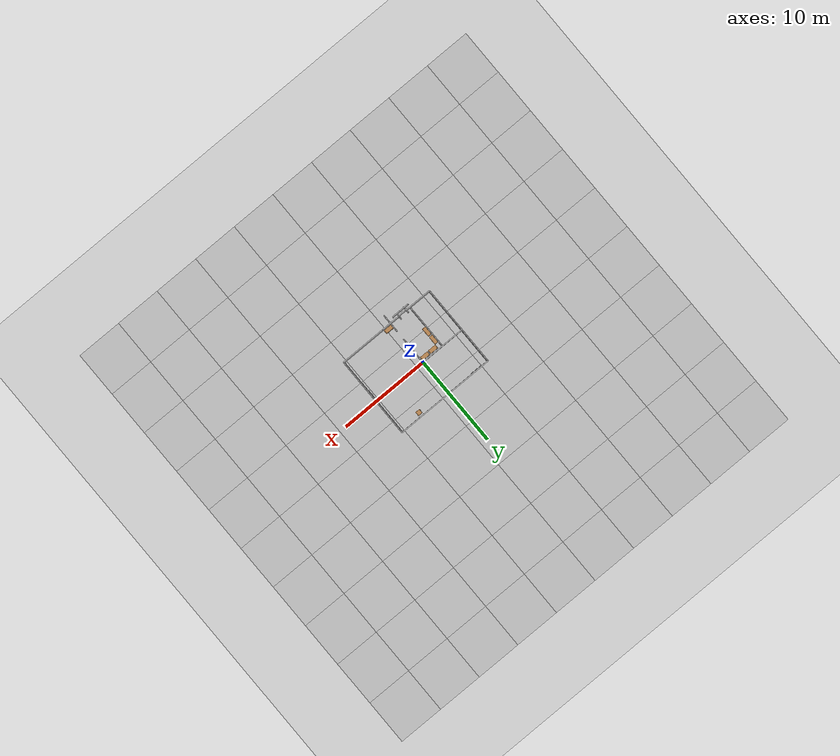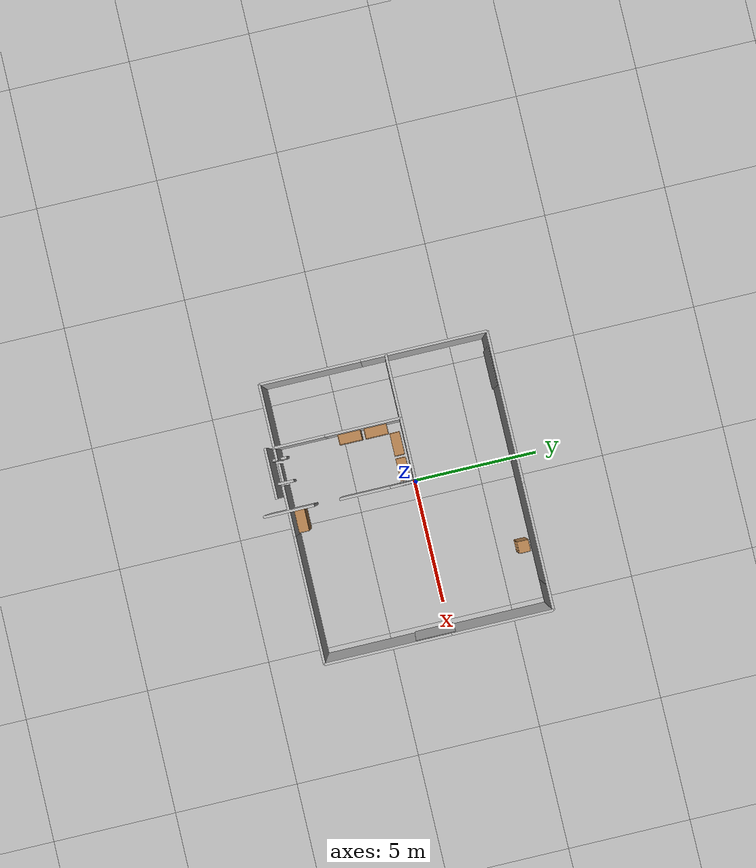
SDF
<sdf version="1.7">
 <world name="default">
  <light name="sun" type="directional">
   <pose>0 0 10 0 -0 0</pose>
   <diffuse>0.8 0.8 0.8 1</diffuse>
   <specular>0.2 0.2 0.2 1</specular>
   <attenuation>
    <range>1000</range>
    <constant>0.9</constant>
    <linear>0.01</linear>
    <quadratic>0.001</quadratic>
   </attenuation>
   <direction>-0.5 0.1 -0.9</direction>
   <spot><inner_angle>0</inner_angle><outer_angle>0</outer_angle><falloff>0</falloff></spot>
  </light>
  <model name="ground_plane">
   <static>1</static>
   <link name="link">
    <collision name="collision">
     <geometry><plane><normal>0 0 1</normal><size>100 100</size></plane></geometry>
     <surface>
      <contact><collide_bitmask>65535</collide_bitmask></contact>
      <friction><ode><mu>100</mu><mu2>50</mu2></ode></friction>
     </surface>
    </collision>
    <visual name="visual">
     <cast_shadows>0</cast_shadows>
     <geometry><plane><normal>0 0 1</normal><size>1 1</size></plane></geometry>
     <material>
      <script><uri>file://media/materials/scripts/gazebo.material</uri><name>Gazebo/Grey</name></script>
     </material>
    </visual>
   </link>
  </model>
  <gravity>0 0 -9.8</gravity>
  <magnetic_field>6e-06 2.3e-05 -4.2e-05</magnetic_field>
  <atmosphere type="adiabatic"/>
  <physics type="ode">
   <max_step_size>0.001</max_step_size>
   <real_time_factor>1</real_time_factor>
   <real_time_update_rate>1000</real_time_update_rate>
  </physics>
  <scene><ambient>0.4 0.4 0.4 1</ambient><background>0.7 0.7 0.7 1</background><shadows>1</shadows></scene>
  <audio><device>default</device></audio>
  <spherical_coordinates>
   <surface_model>EARTH_WGS84</surface_model>
   <latitude_deg>0</latitude_deg>
   <longitude_deg>0</longitude_deg>
   <elevation>0</elevation>
   <heading_deg>0</heading_deg>
  </spherical_coordinates>
  <model name="Bookshelf">
   <static>1</static>
   <link name="link">
    <inertial><mass>1</mass></inertial>
    <collision name="back">
     <pose>0 0.005 0.6 0 -0 0</pose>
     <geometry><box><size>0.9 0.01 1.2</size></box></geometry>
    </collision>
    <visual name="visual1">
     <pose>0 0.005 0.6 0 -0 0</pose>
     <geometry><box><size>0.9 0.01 1.2</size></box></geometry>
     <material>
      <diffuse>1 1 1 1</diffuse>
      <script><uri>file://media/materials/scripts/gazebo.material</uri><name>Gazebo/Wood</name></script>
      <pbr>
       <metal>
        <albedo_map>https://fuel.ignitionrobotics.org/1.0/openrobotics/models/bookshelf/3/files/bookshelf_diffuse.jpg</albedo_map>
       </metal>
      </pbr>
     </material>
    </visual>
    <collision name="left_side">
     <pose>0.45 -0.195 0.6 0 -0 0</pose>
     <geometry><box><size>0.02 0.4 1.2</size></box></geometry>
    </collision>
    <visual name="visual2">
     <pose>0.45 -0.195 0.6 0 -0 0</pose>
     <geometry><box><size>0.02 0.4 1.2</size></box></geometry>
     <material>
      <diffuse>1 1 1 1</diffuse>
      <script><uri>file://media/materials/scripts/gazebo.material</uri><name>Gazebo/Wood</name></script>
      <pbr>
       <metal>
        <albedo_map>https://fuel.ignitionrobotics.org/1.0/openrobotics/models/bookshelf/3/files/bookshelf_diffuse.jpg</albedo_map>
       </metal>
      </pbr>
     </material>
    </visual>
    <collision name="right_side">
     <pose>-0.45 -0.195 0.6 0 -0 0</pose>
     <geometry><box><size>0.02 0.4 1.2</size></box></geometry>
    </collision>
    <visual name="visual3">
     <pose>-0.45 -0.195 0.6 0 -0 0</pose>
     <geometry><box><size>0.02 0.4 1.2</size></box></geometry>
     <material>
      <diffuse>1 1 1 1</diffuse>
      <script><uri>file://media/materials/scripts/gazebo.material</uri><name>Gazebo/Wood</name></script>
      <pbr>
       <metal>
        <albedo_map>https://fuel.ignitionrobotics.org/1.0/openrobotics/models/bookshelf/3/files/bookshelf_diffuse.jpg</albedo_map>
       </metal>
      </pbr>
     </material>
    </visual>
    <collision name="bottom">
     <pose>0 -0.195 0.03 0 -0 0</pose>
     <geometry><box><size>0.88 0.4 0.06</size></box></geometry>
    </collision>
    <visual name="visual4">
     <pose>0 -0.195 0.03 0 -0 0</pose>
     <geometry><box><size>0.88 0.4 0.06</size></box></geometry>
     <material>
      <diffuse>1 1 1 1</diffuse>
      <script><uri>file://media/materials/scripts/gazebo.material</uri><name>Gazebo/Wood</name></script>
      <pbr>
       <metal>
        <albedo_map>https://fuel.ignitionrobotics.org/1.0/openrobotics/models/bookshelf/3/files/bookshelf_diffuse.jpg</albedo_map>
       </metal>
      </pbr>
     </material>
    </visual>
    <collision name="top">
     <pose>0 -0.195 1.19 0 -0 0</pose>
     <geometry><box><size>0.88 0.4 0.02</size></box></geometry>
    </collision>
    <visual name="visual5">
     <pose>0 -0.195 1.19 0 -0 0</pose>
     <geometry><box><size>0.88 0.4 0.02</size></box></geometry>
     <material>
      <diffuse>1 1 1 1</diffuse>
      <script><uri>file://media/materials/scripts/gazebo.material</uri><name>Gazebo/Wood</name></script>
      <pbr>
       <metal>
        <albedo_map>https://fuel.ignitionrobotics.org/1.0/openrobotics/models/bookshelf/3/files/bookshelf_diffuse.jpg</albedo_map>
       </metal>
      </pbr>
     </material>
    </visual>
    <collision name="low_shelf">
     <pose>0 -0.195 0.43 0 -0 0</pose>
     <geometry><box><size>0.88 0.4 0.02</size></box></geometry>
    </collision>
    <visual name="visual6">
     <pose>0 -0.195 0.43 0 -0 0</pose>
     <geometry><box><size>0.88 0.4 0.02</size></box></geometry>
     <material>
      <diffuse>1 1 1 1</diffuse>
      <script><uri>file://media/materials/scripts/gazebo.material</uri><name>Gazebo/Wood</name></script>
      <pbr>
       <metal>
        <albedo_map>https://fuel.ignitionrobotics.org/1.0/openrobotics/models/bookshelf/3/files/bookshelf_diffuse.jpg</albedo_map>
       </metal>
      </pbr>
     </material>
    </visual>
    <collision name="high_shelf">
     <pose>0 -0.195 0.8 0 -0 0</pose>
     <geometry><box><size>0.88 0.4 0.02</size></box></geometry>
    </collision>
    <visual name="visual7">
     <pose>0 -0.195 0.8 0 -0 0</pose>
     <geometry><box><size>0.88 0.4 0.02</size></box></geometry>
     <material>
      <diffuse>1 1 1 1</diffuse>
      <script><uri>file://media/materials/scripts/gazebo.material</uri><name>Gazebo/Wood</name></script>
      <pbr>
       <metal>
        <albedo_map>https://fuel.ignitionrobotics.org/1.0/openrobotics/models/bookshelf/3/files/bookshelf_diffuse.jpg</albedo_map>
       </metal>
      </pbr>
     </material>
    </visual>
   </link>
   <pose>0.48256 -4.48453 0 0 -0 0</pose>
  </model>
  <model name="cabinet">
   <static>1</static>
   <link name="cabinet_bottom_plate">
    <inertial>
     <pose>0 0 -1 0 -0 0</pose>
     <inertia><ixx>2.05</ixx><ixy>0</ixy><ixz>0</ixz><iyy>2.05</iyy><iyz>0</iyz><izz>2.05</izz></inertia>
     <mass>25</mass>
    </inertial>
    <collision name="cabinet_bottom_plate_geom">
     <pose>0 0 0.01 0 -0 0</pose>
     <geometry><box><size>0.45 0.45 0.02</size></box></geometry>
    </collision>
    <visual name="cabinet_bottom_plate_geom_visual">
     <pose>0 0 0.01 0 -0 0</pose>
     <geometry><box><size>0.45 0.45 0.02</size></box></geometry>
     <material>
      <script><uri>file://media/materials/scripts/gazebo.material</uri><name>Gazebo/Wood</name></script>
     </material>
    </visual>
    <collision name="cabinet_bottom_plate_geom_cabinet_back_plate">
     <pose>0.235 0 0.51 0 -0 0</pose>
     <geometry><box><size>0.02 0.45 1.02</size></box></geometry>
    </collision>
    <visual name="cabinet_bottom_plate_geom_cabinet_back_plate_visual">
     <pose>0.235 0 0.51 0 -0 0</pose>
     <geometry><box><size>0.02 0.45 1.02</size></box></geometry>
     <material>
      <script><uri>file://media/materials/scripts/gazebo.material</uri><name>Gazebo/Wood</name></script>
     </material>
    </visual>
    <collision name="cabinet_bottom_plate_geom_cabinet_left_plate">
     <pose>0 0.235 0.51 0 -0 0</pose>
     <geometry><box><size>0.45 0.02 1.02</size></box></geometry>
    </collision>
    <visual name="cabinet_bottom_plate_geom_cabinet_left_plate_visual">
     <pose>0 0.235 0.51 0 -0 0</pose>
     <geometry><box><size>0.45 0.02 1.02</size></box></geometry>
     <material>
      <script><uri>file://media/materials/scripts/gazebo.material</uri><name>Gazebo/Wood</name></script>
     </material>
    </visual>
    <collision name="cabinet_bottom_plate_geom_cabinet_middle_plate">
     <pose>0 0 0.51 0 -0 0</pose>
     <geometry><box><size>0.45 0.45 0.02</size></box></geometry>
    </collision>
    <visual name="cabinet_bottom_plate_geom_cabinet_middle_plate_visual">
     <pose>0 0 0.51 0 -0 0</pose>
     <geometry><box><size>0.45 0.45 0.02</size></box></geometry>
     <material>
      <script><uri>file://media/materials/scripts/gazebo.material</uri><name>Gazebo/Wood</name></script>
     </material>
    </visual>
    <collision name="cabinet_bottom_plate_geom_cabinet_right_plate">
     <pose>0 -0.235 0.51 0 -0 0</pose>
     <geometry><box><size>0.45 0.02 1.02</size></box></geometry>
    </collision>
    <visual name="cabinet_bottom_plate_geom_cabinet_right_plate_visual">
     <pose>0 -0.235 0.51 0 -0 0</pose>
     <geometry><box><size>0.45 0.02 1.02</size></box></geometry>
     <material>
      <script><uri>file://media/materials/scripts/gazebo.material</uri><name>Gazebo/Wood</name></script>
     </material>
    </visual>
    <collision name="cabinet_bottom_plate_geom_cabinet_top_plate">
     <pose>0 0 1.01 0 -0 0</pose>
     <geometry><box><size>0.45 0.45 0.02</size></box></geometry>
    </collision>
    <visual name="cabinet_bottom_plate_geom_cabinet_top_plate_visual">
     <pose>0 0 1.01 0 -0 0</pose>
     <geometry><box><size>0.45 0.45 0.02</size></box></geometry>
     <material>
      <script><uri>file://media/materials/scripts/gazebo.material</uri><name>Gazebo/Wood</name></script>
     </material>
    </visual>
   </link>
   <pose>3.47976 3.55408 0 0 -0 1.5707</pose>
  </model>
  <model name="door_08x2m_0">
   <link name="link">
    <visual name="visual">
     <geometry><box><size>0.1 0.8 2</size></box></geometry>
     <material>
      <script>
       <uri>https://fuel.ignitionrobotics.org/1.0/makerspet/models/door_08x2m/1/files/material/script</uri>
       <uri>https://fuel.ignitionrobotics.org/1.0/makerspet/models/door_08x2m/1/files/material/textures</uri>
       <name>Custom/door_08x2m</name>
      </script>
     </material>
    </visual>
   </link>
   <static>1</static>
   <pose>-1.11355 -5.04411 0 0 -0 0</pose>
  </model>
  <model name="living_room"><static>0</static><pose>-1.83596 1.40391 0 0 -0 0</pose></model>
  <model name="room_wall_2x5">
   <link name="link">
    <visual name="visual">
     <geometry><box><size>0.1 5 2</size></box></geometry>
     <material>
      <script>
       <uri>https://fuel.ignitionrobotics.org/1.0/makerspet/models/room_wall_2x5m/1/files/material/script</uri>
       <uri>https://fuel.ignitionrobotics.org/1.0/makerspet/models/room_wall_2x5m/1/files/material/textures</uri>
       <name>Custom/room_wall_2x5</name>
      </script>
     </material>
    </visual>
    <collision name="collision"><geometry><box><size>0.1 5 2</size></box></geometry></collision>
   </link>
   <static>1</static>
   <pose>6 -2.5 1 0 -0 0</pose>
  </model>
  <model name="room_wall_2x5_0">
   <link name="link">
    <visual name="visual">
     <geometry><box><size>0.1 5 2</size></box></geometry>
     <material>
      <script>
       <uri>https://fuel.ignitionrobotics.org/1.0/makerspet/models/room_wall_2x5m/1/files/material/script</uri>
       <uri>https://fuel.ignitionrobotics.org/1.0/makerspet/models/room_wall_2x5m/1/files/material/textures</uri>
       <name>Custom/room_wall_2x5</name>
      </script>
     </material>
    </visual>
    <collision name="collision"><geometry><box><size>0.1 5 2</size></box></geometry></collision>
   </link>
   <static>1</static>
   <pose>6 1.5 1 0 -0 0</pose>
  </model>
  <model name="room_wall_2x5_1">
   <link name="link">
    <visual name="visual">
     <geometry><box><size>0.1 5 2</size></box></geometry>
     <material>
      <script>
       <uri>https://fuel.ignitionrobotics.org/1.0/makerspet/models/room_wall_2x5m/1/files/material/script</uri>
       <uri>https://fuel.ignitionrobotics.org/1.0/makerspet/models/room_wall_2x5m/1/files/material/textures</uri>
       <name>Custom/room_wall_2x5</name>
      </script>
     </material>
    </visual>
    <collision name="collision"><geometry><box><size>0.1 5 2</size></box></geometry></collision>
   </link>
   <static>1</static>
   <pose>3.5 -5 1 0 -0 1.5707</pose>
  </model>
  <model name="window_curtains">
   <link name="link">
    <visual name="visual">
     <geometry><box><size>0.02 1.5676 2</size></box></geometry>
     <material>
      <script>
       <uri>https://fuel.ignitionrobotics.org/1.0/makerspet/models/window_curtains/1/files/material/script</uri>
       <uri>https://fuel.ignitionrobotics.org/1.0/makerspet/models/window_curtains/1/files/material/textures</uri>
       <name>Custom/window_curtains</name>
      </script>
      <emissive>0 1 0 1</emissive>
     </material>
    </visual>
   </link>
   <static>1</static>
   <pose>5.92005 -0.610208 1 0 -0 0</pose>
  </model>
  <model name="window_curtains_0">
   <link name="link">
    <visual name="visual">
     <geometry><box><size>0.02 1.5676 2</size></box></geometry>
     <material>
      <script>
       <uri>https://fuel.ignitionrobotics.org/1.0/makerspet/models/window_curtains/1/files/material/script</uri>
       <uri>https://fuel.ignitionrobotics.org/1.0/makerspet/models/window_curtains/1/files/material/textures</uri>
       <name>Custom/window_curtains</name>
      </script>
      <emissive>0 1 0 1</emissive>
     </material>
    </visual>
   </link>
   <static>1</static>
   <pose>-3.64443 3.90072 1 0 -0 1.5707</pose>
  </model>
  <model name="room_wall_2x5_2_clone">
   <link name="link">
    <visual name="visual">
     <geometry><box><size>0.1 5 2</size></box></geometry>
     <material>
      <script>
       <uri>https://fuel.ignitionrobotics.org/1.0/makerspet/models/room_wall_2x5m/1/files/material/script</uri>
       <uri>https://fuel.ignitionrobotics.org/1.0/makerspet/models/room_wall_2x5m/1/files/material/textures</uri>
       <name>Custom/room_wall_2x5</name>
      </script>
     </material>
    </visual>
    <collision name="collision"><geometry><box><size>0.1 5 2</size></box></geometry></collision>
   </link>
   <static>1</static>
   <pose>3.5 4 1 0 -0 1.5707</pose>
  </model>
  <model name="room_wall_2x5_2_clone_clone">
   <link name="link">
    <visual name="visual">
     <geometry><box><size>0.1 5 2</size></box></geometry>
     <material>
      <script>
       <uri>https://fuel.ignitionrobotics.org/1.0/makerspet/models/room_wall_2x5m/1/files/material/script</uri>
       <uri>https://fuel.ignitionrobotics.org/1.0/makerspet/models/room_wall_2x5m/1/files/material/textures</uri>
       <name>Custom/room_wall_2x5</name>
      </script>
     </material>
    </visual>
    <collision name="collision"><geometry><box><size>0.1 5 2</size></box></geometry></collision>
   </link>
   <static>1</static>
   <pose>2.5 4 1 0 -0 1.5707</pose>
  </model>
  <model name="door_08x2m">
   <link name="link">
    <visual name="visual">
     <geometry><box><size>0.1 0.8 2</size></box></geometry>
     <material>
      <script>
       <uri>https://fuel.gazebosim.org/1.0/makerspet/models/door_08x2m/1/files/material/script</uri>
       <uri>https://fuel.gazebosim.org/1.0/makerspet/models/door_08x2m/1/files/material/textures</uri>
       <name>Custom/door_08x2m</name>
      </script>
     </material>
    </visual>
   </link>
   <static>1</static>
   <pose>-1.50001 -5.0675 0 0 -0 1.5707</pose>
  </model>
  <model name="room_wall_2x2">
   <link name="link">
    <visual name="visual">
     <geometry><box><size>0.1 2 2</size></box></geometry>
     <material>
      <script>
       <uri>https://fuel.ignitionrobotics.org/1.0/makerspet/models/room_wall_2x5m/1/files/material/script</uri>
       <uri>https://fuel.ignitionrobotics.org/1.0/makerspet/models/room_wall_2x5m/1/files/material/textures</uri>
       <name>Custom/room_wall_2x5</name>
      </script>
     </material>
    </visual>
    <collision name="collision"><geometry><box><size>0.1 2 2</size></box></geometry></collision>
   </link>
   <static>1</static>
   <pose>0 3 1 0 -0 0</pose>
  </model>
  <model name="room_wall_2x5_2_clone_clone_clone">
   <link name="link">
    <visual name="visual">
     <geometry><box><size>0.1 5 2</size></box></geometry>
     <material>
      <script>
       <uri>https://fuel.ignitionrobotics.org/1.0/makerspet/models/room_wall_2x5m/1/files/material/script</uri>
       <uri>https://fuel.ignitionrobotics.org/1.0/makerspet/models/room_wall_2x5m/1/files/material/textures</uri>
       <name>Custom/room_wall_2x5</name>
      </script>
     </material>
    </visual>
    <collision name="collision"><geometry><box><size>0.1 5 2</size></box></geometry></collision>
   </link>
   <static>1</static>
   <pose>-2.5 4 1 0 -0 1.5707</pose>
  </model>
  <model name="room_wall_2x5_2_clone_clone_clone_0">
   <link name="link">
    <visual name="visual">
     <geometry><box><size>0.1 5 2</size></box></geometry>
     <material>
      <script>
       <uri>https://fuel.ignitionrobotics.org/1.0/makerspet/models/room_wall_2x5m/1/files/material/script</uri>
       <uri>https://fuel.ignitionrobotics.org/1.0/makerspet/models/room_wall_2x5m/1/files/material/textures</uri>
       <name>Custom/room_wall_2x5</name>
      </script>
     </material>
    </visual>
    <collision name="collision"><geometry><box><size>0.1 5 2</size></box></geometry></collision>
   </link>
   <static>1</static>
   <pose>-5 1.5 1 0 -0 0</pose>
  </model>
  <model name="room_wall_2x2_clone">
   <link name="link">
    <visual name="visual">
     <geometry><box><size>0.1 3 2</size></box></geometry>
     <material>
      <script>
       <uri>https://fuel.ignitionrobotics.org/1.0/makerspet/models/room_wall_2x5m/1/files/material/script</uri>
       <uri>https://fuel.ignitionrobotics.org/1.0/makerspet/models/room_wall_2x5m/1/files/material/textures</uri>
       <name>Custom/room_wall_2x5</name>
      </script>
     </material>
    </visual>
    <collision name="collision"><geometry><box><size>0.1 3 2</size></box></geometry></collision>
   </link>
   <static>1</static>
   <pose>0 -1.5 1 0 -0 0</pose>
  </model>
  <model name="room_wall_2x2_clone_clone_clone">
   <link name="link">
    <visual name="visual">
     <geometry><box><size>0.1 3 2</size></box></geometry>
     <material>
      <script>
       <uri>https://fuel.ignitionrobotics.org/1.0/makerspet/models/room_wall_2x5m/1/files/material/script</uri>
       <uri>https://fuel.ignitionrobotics.org/1.0/makerspet/models/room_wall_2x5m/1/files/material/textures</uri>
       <name>Custom/room_wall_2x5</name>
      </script>
     </material>
    </visual>
    <collision name="collision"><geometry><box><size>0.1 3 2</size></box></geometry></collision>
   </link>
   <static>1</static>
   <pose>-3.5 -5 1 0 -0 1.5707</pose>
  </model>
  <model name="door_08x2m_0_clone">
   <link name="link">
    <visual name="visual">
     <geometry><box><size>0.1 0.8 2</size></box></geometry>
     <material>
      <script>
       <uri>https://fuel.ignitionrobotics.org/1.0/makerspet/models/door_08x2m/1/files/material/script</uri>
       <uri>https://fuel.ignitionrobotics.org/1.0/makerspet/models/door_08x2m/1/files/material/textures</uri>
       <name>Custom/door_08x2m</name>
      </script>
     </material>
    </visual>
   </link>
   <static>1</static>
   <pose>-2.06337 -5.11198 0 0 -0 0</pose>
  </model>
  <model name="Bookshelf_clone">
   <static>1</static>
   <link name="link">
    <inertial><mass>1</mass></inertial>
    <collision name="back">
     <pose>0 0.005 0.6 0 -0 0</pose>
     <geometry><box><size>0.9 0.01 1.2</size></box></geometry>
    </collision>
    <visual name="visual1">
     <pose>0 0.005 0.6 0 -0 0</pose>
     <geometry><box><size>0.9 0.01 1.2</size></box></geometry>
     <material>
      <diffuse>1 1 1 1</diffuse>
      <script><uri>file://media/materials/scripts/gazebo.material</uri><name>Gazebo/Wood</name></script>
      <pbr>
       <metal>
        <albedo_map>https://fuel.ignitionrobotics.org/1.0/openrobotics/models/bookshelf/3/files/bookshelf_diffuse.jpg</albedo_map>
       </metal>
      </pbr>
     </material>
    </visual>
    <collision name="left_side">
     <pose>0.45 -0.195 0.6 0 -0 0</pose>
     <geometry><box><size>0.02 0.4 1.2</size></box></geometry>
    </collision>
    <visual name="visual2">
     <pose>0.45 -0.195 0.6 0 -0 0</pose>
     <geometry><box><size>0.02 0.4 1.2</size></box></geometry>
     <material>
      <diffuse>1 1 1 1</diffuse>
      <script><uri>file://media/materials/scripts/gazebo.material</uri><name>Gazebo/Wood</name></script>
      <pbr>
       <metal>
        <albedo_map>https://fuel.ignitionrobotics.org/1.0/openrobotics/models/bookshelf/3/files/bookshelf_diffuse.jpg</albedo_map>
       </metal>
      </pbr>
     </material>
    </visual>
    <collision name="right_side">
     <pose>-0.45 -0.195 0.6 0 -0 0</pose>
     <geometry><box><size>0.02 0.4 1.2</size></box></geometry>
    </collision>
    <visual name="visual3">
     <pose>-0.45 -0.195 0.6 0 -0 0</pose>
     <geometry><box><size>0.02 0.4 1.2</size></box></geometry>
     <material>
      <diffuse>1 1 1 1</diffuse>
      <script><uri>file://media/materials/scripts/gazebo.material</uri><name>Gazebo/Wood</name></script>
      <pbr>
       <metal>
        <albedo_map>https://fuel.ignitionrobotics.org/1.0/openrobotics/models/bookshelf/3/files/bookshelf_diffuse.jpg</albedo_map>
       </metal>
      </pbr>
     </material>
    </visual>
    <collision name="bottom">
     <pose>0 -0.195 0.03 0 -0 0</pose>
     <geometry><box><size>0.88 0.4 0.06</size></box></geometry>
    </collision>
    <visual name="visual4">
     <pose>0 -0.195 0.03 0 -0 0</pose>
     <geometry><box><size>0.88 0.4 0.06</size></box></geometry>
     <material>
      <diffuse>1 1 1 1</diffuse>
      <script><uri>file://media/materials/scripts/gazebo.material</uri><name>Gazebo/Wood</name></script>
      <pbr>
       <metal>
        <albedo_map>https://fuel.ignitionrobotics.org/1.0/openrobotics/models/bookshelf/3/files/bookshelf_diffuse.jpg</albedo_map>
       </metal>
      </pbr>
     </material>
    </visual>
    <collision name="top">
     <pose>0 -0.195 1.19 0 -0 0</pose>
     <geometry><box><size>0.88 0.4 0.02</size></box></geometry>
    </collision>
    <visual name="visual5">
     <pose>0 -0.195 1.19 0 -0 0</pose>
     <geometry><box><size>0.88 0.4 0.02</size></box></geometry>
     <material>
      <diffuse>1 1 1 1</diffuse>
      <script><uri>file://media/materials/scripts/gazebo.material</uri><name>Gazebo/Wood</name></script>
      <pbr>
       <metal>
        <albedo_map>https://fuel.ignitionrobotics.org/1.0/openrobotics/models/bookshelf/3/files/bookshelf_diffuse.jpg</albedo_map>
       </metal>
      </pbr>
     </material>
    </visual>
    <collision name="low_shelf">
     <pose>0 -0.195 0.43 0 -0 0</pose>
     <geometry><box><size>0.88 0.4 0.02</size></box></geometry>
    </collision>
    <visual name="visual6">
     <pose>0 -0.195 0.43 0 -0 0</pose>
     <geometry><box><size>0.88 0.4 0.02</size></box></geometry>
     <material>
      <diffuse>1 1 1 1</diffuse>
      <script><uri>file://media/materials/scripts/gazebo.material</uri><name>Gazebo/Wood</name></script>
      <pbr>
       <metal>
        <albedo_map>https://fuel.ignitionrobotics.org/1.0/openrobotics/models/bookshelf/3/files/bookshelf_diffuse.jpg</albedo_map>
       </metal>
      </pbr>
     </material>
    </visual>
    <collision name="high_shelf">
     <pose>0 -0.195 0.8 0 -0 0</pose>
     <geometry><box><size>0.88 0.4 0.02</size></box></geometry>
    </collision>
    <visual name="visual7">
     <pose>0 -0.195 0.8 0 -0 0</pose>
     <geometry><box><size>0.88 0.4 0.02</size></box></geometry>
     <material>
      <diffuse>1 1 1 1</diffuse>
      <script><uri>file://media/materials/scripts/gazebo.material</uri><name>Gazebo/Wood</name></script>
      <pbr>
       <metal>
        <albedo_map>https://fuel.ignitionrobotics.org/1.0/openrobotics/models/bookshelf/3/files/bookshelf_diffuse.jpg</albedo_map>
       </metal>
      </pbr>
     </material>
    </visual>
   </link>
   <pose>-0.566576 -0.161307 0 0 -0 0</pose>
  </model>
  <model name="Bookshelf_clone_0">
   <static>1</static>
   <link name="link">
    <inertial><mass>1</mass></inertial>
    <collision name="back">
     <pose>0 0.005 0.6 0 -0 0</pose>
     <geometry><box><size>0.9 0.01 1.2</size></box></geometry>
    </collision>
    <visual name="visual1">
     <pose>0 0.005 0.6 0 -0 0</pose>
     <geometry><box><size>0.9 0.01 1.2</size></box></geometry>
     <material>
      <diffuse>1 1 1 1</diffuse>
      <script><uri>file://media/materials/scripts/gazebo.material</uri><name>Gazebo/Wood</name></script>
      <pbr>
       <metal>
        <albedo_map>https://fuel.ignitionrobotics.org/1.0/openrobotics/models/bookshelf/3/files/bookshelf_diffuse.jpg</albedo_map>
       </metal>
      </pbr>
     </material>
    </visual>
    <collision name="left_side">
     <pose>0.45 -0.195 0.6 0 -0 0</pose>
     <geometry><box><size>0.02 0.4 1.2</size></box></geometry>
    </collision>
    <visual name="visual2">
     <pose>0.45 -0.195 0.6 0 -0 0</pose>
     <geometry><box><size>0.02 0.4 1.2</size></box></geometry>
     <material>
      <diffuse>1 1 1 1</diffuse>
      <script><uri>file://media/materials/scripts/gazebo.material</uri><name>Gazebo/Wood</name></script>
      <pbr>
       <metal>
        <albedo_map>https://fuel.ignitionrobotics.org/1.0/openrobotics/models/bookshelf/3/files/bookshelf_diffuse.jpg</albedo_map>
       </metal>
      </pbr>
     </material>
    </visual>
    <collision name="right_side">
     <pose>-0.45 -0.195 0.6 0 -0 0</pose>
     <geometry><box><size>0.02 0.4 1.2</size></box></geometry>
    </collision>
    <visual name="visual3">
     <pose>-0.45 -0.195 0.6 0 -0 0</pose>
     <geometry><box><size>0.02 0.4 1.2</size></box></geometry>
     <material>
      <diffuse>1 1 1 1</diffuse>
      <script><uri>file://media/materials/scripts/gazebo.material</uri><name>Gazebo/Wood</name></script>
      <pbr>
       <metal>
        <albedo_map>https://fuel.ignitionrobotics.org/1.0/openrobotics/models/bookshelf/3/files/bookshelf_diffuse.jpg</albedo_map>
       </metal>
      </pbr>
     </material>
    </visual>
    <collision name="bottom">
     <pose>0 -0.195 0.03 0 -0 0</pose>
     <geometry><box><size>0.88 0.4 0.06</size></box></geometry>
    </collision>
    <visual name="visual4">
     <pose>0 -0.195 0.03 0 -0 0</pose>
     <geometry><box><size>0.88 0.4 0.06</size></box></geometry>
     <material>
      <diffuse>1 1 1 1</diffuse>
      <script><uri>file://media/materials/scripts/gazebo.material</uri><name>Gazebo/Wood</name></script>
      <pbr>
       <metal>
        <albedo_map>https://fuel.ignitionrobotics.org/1.0/openrobotics/models/bookshelf/3/files/bookshelf_diffuse.jpg</albedo_map>
       </metal>
      </pbr>
     </material>
    </visual>
    <collision name="top">
     <pose>0 -0.195 1.19 0 -0 0</pose>
     <geometry><box><size>0.88 0.4 0.02</size></box></geometry>
    </collision>
    <visual name="visual5">
     <pose>0 -0.195 1.19 0 -0 0</pose>
     <geometry><box><size>0.88 0.4 0.02</size></box></geometry>
     <material>
      <diffuse>1 1 1 1</diffuse>
      <script><uri>file://media/materials/scripts/gazebo.material</uri><name>Gazebo/Wood</name></script>
      <pbr>
       <metal>
        <albedo_map>https://fuel.ignitionrobotics.org/1.0/openrobotics/models/bookshelf/3/files/bookshelf_diffuse.jpg</albedo_map>
       </metal>
      </pbr>
     </material>
    </visual>
    <collision name="low_shelf">
     <pose>0 -0.195 0.43 0 -0 0</pose>
     <geometry><box><size>0.88 0.4 0.02</size></box></geometry>
    </collision>
    <visual name="visual6">
     <pose>0 -0.195 0.43 0 -0 0</pose>
     <geometry><box><size>0.88 0.4 0.02</size></box></geometry>
     <material>
      <diffuse>1 1 1 1</diffuse>
      <script><uri>file://media/materials/scripts/gazebo.material</uri><name>Gazebo/Wood</name></script>
      <pbr>
       <metal>
        <albedo_map>https://fuel.ignitionrobotics.org/1.0/openrobotics/models/bookshelf/3/files/bookshelf_diffuse.jpg</albedo_map>
       </metal>
      </pbr>
     </material>
    </visual>
    <collision name="high_shelf">
     <pose>0 -0.195 0.8 0 -0 0</pose>
     <geometry><box><size>0.88 0.4 0.02</size></box></geometry>
    </collision>
    <visual name="visual7">
     <pose>0 -0.195 0.8 0 -0 0</pose>
     <geometry><box><size>0.88 0.4 0.02</size></box></geometry>
     <material>
      <diffuse>1 1 1 1</diffuse>
      <script><uri>file://media/materials/scripts/gazebo.material</uri><name>Gazebo/Wood</name></script>
      <pbr>
       <metal>
        <albedo_map>https://fuel.ignitionrobotics.org/1.0/openrobotics/models/bookshelf/3/files/bookshelf_diffuse.jpg</albedo_map>
       </metal>
      </pbr>
     </material>
    </visual>
   </link>
   <pose>-1.58295 -0.16309 0 0 -0 0</pose>
  </model>
  <model name="Bookshelf_clone_1">
   <static>1</static>
   <link name="link">
    <inertial><mass>1</mass></inertial>
    <collision name="back">
     <pose>0 0.005 0.6 0 -0 0</pose>
     <geometry><box><size>0.9 0.01 1.2</size></box></geometry>
    </collision>
    <visual name="visual1">
     <pose>0 0.005 0.6 0 -0 0</pose>
     <geometry><box><size>0.9 0.01 1.2</size></box></geometry>
     <material>
      <diffuse>1 1 1 1</diffuse>
      <script><uri>file://media/materials/scripts/gazebo.material</uri><name>Gazebo/Wood</name></script>
      <pbr>
       <metal>
        <albedo_map>https://fuel.ignitionrobotics.org/1.0/openrobotics/models/bookshelf/3/files/bookshelf_diffuse.jpg</albedo_map>
       </metal>
      </pbr>
     </material>
    </visual>
    <collision name="left_side">
     <pose>0.45 -0.195 0.6 0 -0 0</pose>
     <geometry><box><size>0.02 0.4 1.2</size></box></geometry>
    </collision>
    <visual name="visual2">
     <pose>0.45 -0.195 0.6 0 -0 0</pose>
     <geometry><box><size>0.02 0.4 1.2</size></box></geometry>
     <material>
      <diffuse>1 1 1 1</diffuse>
      <script><uri>file://media/materials/scripts/gazebo.material</uri><name>Gazebo/Wood</name></script>
      <pbr>
       <metal>
        <albedo_map>https://fuel.ignitionrobotics.org/1.0/openrobotics/models/bookshelf/3/files/bookshelf_diffuse.jpg</albedo_map>
       </metal>
      </pbr>
     </material>
    </visual>
    <collision name="right_side">
     <pose>-0.45 -0.195 0.6 0 -0 0</pose>
     <geometry><box><size>0.02 0.4 1.2</size></box></geometry>
    </collision>
    <visual name="visual3">
     <pose>-0.45 -0.195 0.6 0 -0 0</pose>
     <geometry><box><size>0.02 0.4 1.2</size></box></geometry>
     <material>
      <diffuse>1 1 1 1</diffuse>
      <script><uri>file://media/materials/scripts/gazebo.material</uri><name>Gazebo/Wood</name></script>
      <pbr>
       <metal>
        <albedo_map>https://fuel.ignitionrobotics.org/1.0/openrobotics/models/bookshelf/3/files/bookshelf_diffuse.jpg</albedo_map>
       </metal>
      </pbr>
     </material>
    </visual>
    <collision name="bottom">
     <pose>0 -0.195 0.03 0 -0 0</pose>
     <geometry><box><size>0.88 0.4 0.06</size></box></geometry>
    </collision>
    <visual name="visual4">
     <pose>0 -0.195 0.03 0 -0 0</pose>
     <geometry><box><size>0.88 0.4 0.06</size></box></geometry>
     <material>
      <diffuse>1 1 1 1</diffuse>
      <script><uri>file://media/materials/scripts/gazebo.material</uri><name>Gazebo/Wood</name></script>
      <pbr>
       <metal>
        <albedo_map>https://fuel.ignitionrobotics.org/1.0/openrobotics/models/bookshelf/3/files/bookshelf_diffuse.jpg</albedo_map>
       </metal>
      </pbr>
     </material>
    </visual>
    <collision name="top">
     <pose>0 -0.195 1.19 0 -0 0</pose>
     <geometry><box><size>0.88 0.4 0.02</size></box></geometry>
    </collision>
    <visual name="visual5">
     <pose>0 -0.195 1.19 0 -0 0</pose>
     <geometry><box><size>0.88 0.4 0.02</size></box></geometry>
     <material>
      <diffuse>1 1 1 1</diffuse>
      <script><uri>file://media/materials/scripts/gazebo.material</uri><name>Gazebo/Wood</name></script>
      <pbr>
       <metal>
        <albedo_map>https://fuel.ignitionrobotics.org/1.0/openrobotics/models/bookshelf/3/files/bookshelf_diffuse.jpg</albedo_map>
       </metal>
      </pbr>
     </material>
    </visual>
    <collision name="low_shelf">
     <pose>0 -0.195 0.43 0 -0 0</pose>
     <geometry><box><size>0.88 0.4 0.02</size></box></geometry>
    </collision>
    <visual name="visual6">
     <pose>0 -0.195 0.43 0 -0 0</pose>
     <geometry><box><size>0.88 0.4 0.02</size></box></geometry>
     <material>
      <diffuse>1 1 1 1</diffuse>
      <script><uri>file://media/materials/scripts/gazebo.material</uri><name>Gazebo/Wood</name></script>
      <pbr>
       <metal>
        <albedo_map>https://fuel.ignitionrobotics.org/1.0/openrobotics/models/bookshelf/3/files/bookshelf_diffuse.jpg</albedo_map>
       </metal>
      </pbr>
     </material>
    </visual>
    <collision name="high_shelf">
     <pose>0 -0.195 0.8 0 -0 0</pose>
     <geometry><box><size>0.88 0.4 0.02</size></box></geometry>
    </collision>
    <visual name="visual7">
     <pose>0 -0.195 0.8 0 -0 0</pose>
     <geometry><box><size>0.88 0.4 0.02</size></box></geometry>
     <material>
      <diffuse>1 1 1 1</diffuse>
      <script><uri>file://media/materials/scripts/gazebo.material</uri><name>Gazebo/Wood</name></script>
      <pbr>
       <metal>
        <albedo_map>https://fuel.ignitionrobotics.org/1.0/openrobotics/models/bookshelf/3/files/bookshelf_diffuse.jpg</albedo_map>
       </metal>
      </pbr>
     </material>
    </visual>
   </link>
   <pose>-2.4561 -1.04839 0 0 -0 1.5707</pose>
  </model>
  <model name="room_wall_2x2_clone_clone_clone_0">
   <link name="link">
    <visual name="visual">
     <geometry><box><size>0.1 3 2</size></box></geometry>
     <material>
      <script>
       <uri>https://fuel.ignitionrobotics.org/1.0/makerspet/models/room_wall_2x5m/1/files/material/script</uri>
       <uri>https://fuel.ignitionrobotics.org/1.0/makerspet/models/room_wall_2x5m/1/files/material/textures</uri>
       <name>Custom/room_wall_2x5</name>
      </script>
     </material>
    </visual>
    <collision name="collision"><geometry><box><size>0.1 3 2</size></box></geometry></collision>
   </link>
   <static>1</static>
   <pose>-2.5 -1.5 1 0 -0 0</pose>
  </model>
  <model name="room_wall_2x2_clone_0">
   <link name="link">
    <visual name="visual">
     <geometry><box><size>0.1 2 2</size></box></geometry>
     <material>
      <script>
       <uri>https://fuel.ignitionrobotics.org/1.0/makerspet/models/room_wall_2x5m/1/files/material/script</uri>
       <uri>https://fuel.ignitionrobotics.org/1.0/makerspet/models/room_wall_2x5m/1/files/material/textures</uri>
       <name>Custom/room_wall_2x5</name>
      </script>
     </material>
    </visual>
    <collision name="collision"><geometry><box><size>0.1 2 2</size></box></geometry></collision>
   </link>
   <static>1</static>
   <pose>0 -5 1 0 -0 1.5707</pose>
  </model>
  <model name="room_wall_2x5_2_clone_clone_clone_0_clone">
   <link name="link">
    <visual name="visual">
     <geometry><box><size>0.1 5 2</size></box></geometry>
     <material>
      <script>
       <uri>https://fuel.ignitionrobotics.org/1.0/makerspet/models/room_wall_2x5m/1/files/material/script</uri>
       <uri>https://fuel.ignitionrobotics.org/1.0/makerspet/models/room_wall_2x5m/1/files/material/textures</uri>
       <name>Custom/room_wall_2x5</name>
      </script>
     </material>
    </visual>
    <collision name="collision"><geometry><box><size>0.1 5 2</size></box></geometry></collision>
   </link>
   <static>1</static>
   <pose>-5 -2.5 1 0 -0 0</pose>
  </model>
  <model name="room_wall_2x5_2_clone_clone_clone_clone">
   <link name="link">
    <visual name="visual">
     <geometry><box><size>0.1 5 2</size></box></geometry>
     <material>
      <script>
       <uri>https://fuel.ignitionrobotics.org/1.0/makerspet/models/room_wall_2x5m/1/files/material/script</uri>
       <uri>https://fuel.ignitionrobotics.org/1.0/makerspet/models/room_wall_2x5m/1/files/material/textures</uri>
       <name>Custom/room_wall_2x5</name>
      </script>
     </material>
    </visual>
    <collision name="collision"><geometry><box><size>0.1 5 2</size></box></geometry></collision>
   </link>
   <static>1</static>
   <pose>-2.5 0 1 0 -0 1.5707</pose>
  </model>
  <model name="room_wall_2x2_clone_0_clone">
   <link name="link">
    <visual name="visual">
     <geometry><box><size>0.1 2 2</size></box></geometry>
     <material>
      <script>
       <uri>https://fuel.ignitionrobotics.org/1.0/makerspet/models/room_wall_2x5m/1/files/material/script</uri>
       <uri>https://fuel.ignitionrobotics.org/1.0/makerspet/models/room_wall_2x5m/1/files/material/textures</uri>
       <name>Custom/room_wall_2x5</name>
      </script>
     </material>
    </visual>
    <collision name="collision"><geometry><box><size>0.1 2 2</size></box></geometry></collision>
   </link>
   <static>1</static>
   <pose>0 -5 1 0 -0 0</pose>
  </model>
  <model name="room_wall_2x2_clone_0_clone_clone">
   <link name="link">
    <visual name="visual">
     <geometry><box><size>0.1 2 2</size></box></geometry>
     <material>
      <script>
       <uri>https://fuel.ignitionrobotics.org/1.0/makerspet/models/room_wall_2x5m/1/files/material/script</uri>
       <uri>https://fuel.ignitionrobotics.org/1.0/makerspet/models/room_wall_2x5m/1/files/material/textures</uri>
       <name>Custom/room_wall_2x5</name>
      </script>
     </material>
    </visual>
    <collision name="collision"><geometry><box><size>0.1 2 2</size></box></geometry></collision>
   </link>
   <static>1</static>
   <pose>-2.5 -4 1 0 -0 0</pose>
  </model>
  <model name="room_wall_2x2_clone_1">
   <link name="link">
    <visual name="visual">
     <geometry><box><size>0.1 2 2</size></box></geometry>
     <material>
      <script>
       <uri>https://fuel.ignitionrobotics.org/1.0/makerspet/models/room_wall_2x5m/1/files/material/script</uri>
       <uri>https://fuel.ignitionrobotics.org/1.0/makerspet/models/room_wall_2x5m/1/files/material/textures</uri>
       <name>Custom/room_wall_2x5</name>
      </script>
     </material>
    </visual>
    <collision name="collision"><geometry><box><size>0.1 2 2</size></box></geometry></collision>
   </link>
   <static>1</static>
   <pose>0 0 1 0 -0 0</pose>
  </model>
  <model name="Bookshelf_clone_1_clone">
   <static>1</static>
   <link name="link">
    <inertial><mass>1</mass></inertial>
    <collision name="back">
     <pose>0 0.005 0.6 0 -0 0</pose>
     <geometry><box><size>0.9 0.01 1.2</size></box></geometry>
    </collision>
    <visual name="visual1">
     <pose>0 0.005 0.6 0 -0 0</pose>
     <geometry><box><size>0.9 0.01 1.2</size></box></geometry>
     <material>
      <diffuse>1 1 1 1</diffuse>
      <script><uri>file://media/materials/scripts/gazebo.material</uri><name>Gazebo/Wood</name></script>
      <pbr>
       <metal>
        <albedo_map>https://fuel.ignitionrobotics.org/1.0/openrobotics/models/bookshelf/3/files/bookshelf_diffuse.jpg</albedo_map>
       </metal>
      </pbr>
     </material>
    </visual>
    <collision name="left_side">
     <pose>0.45 -0.195 0.6 0 -0 0</pose>
     <geometry><box><size>0.02 0.4 1.2</size></box></geometry>
    </collision>
    <visual name="visual2">
     <pose>0.45 -0.195 0.6 0 -0 0</pose>
     <geometry><box><size>0.02 0.4 1.2</size></box></geometry>
     <material>
      <diffuse>1 1 1 1</diffuse>
      <script><uri>file://media/materials/scripts/gazebo.material</uri><name>Gazebo/Wood</name></script>
      <pbr>
       <metal>
        <albedo_map>https://fuel.ignitionrobotics.org/1.0/openrobotics/models/bookshelf/3/files/bookshelf_diffuse.jpg</albedo_map>
       </metal>
      </pbr>
     </material>
    </visual>
    <collision name="right_side">
     <pose>-0.45 -0.195 0.6 0 -0 0</pose>
     <geometry><box><size>0.02 0.4 1.2</size></box></geometry>
    </collision>
    <visual name="visual3">
     <pose>-0.45 -0.195 0.6 0 -0 0</pose>
     <geometry><box><size>0.02 0.4 1.2</size></box></geometry>
     <material>
      <diffuse>1 1 1 1</diffuse>
      <script><uri>file://media/materials/scripts/gazebo.material</uri><name>Gazebo/Wood</name></script>
      <pbr>
       <metal>
        <albedo_map>https://fuel.ignitionrobotics.org/1.0/openrobotics/models/bookshelf/3/files/bookshelf_diffuse.jpg</albedo_map>
       </metal>
      </pbr>
     </material>
    </visual>
    <collision name="bottom">
     <pose>0 -0.195 0.03 0 -0 0</pose>
     <geometry><box><size>0.88 0.4 0.06</size></box></geometry>
    </collision>
    <visual name="visual4">
     <pose>0 -0.195 0.03 0 -0 0</pose>
     <geometry><box><size>0.88 0.4 0.06</size></box></geometry>
     <material>
      <diffuse>1 1 1 1</diffuse>
      <script><uri>file://media/materials/scripts/gazebo.material</uri><name>Gazebo/Wood</name></script>
      <pbr>
       <metal>
        <albedo_map>https://fuel.ignitionrobotics.org/1.0/openrobotics/models/bookshelf/3/files/bookshelf_diffuse.jpg</albedo_map>
       </metal>
      </pbr>
     </material>
    </visual>
    <collision name="top">
     <pose>0 -0.195 1.19 0 -0 0</pose>
     <geometry><box><size>0.88 0.4 0.02</size></box></geometry>
    </collision>
    <visual name="visual5">
     <pose>0 -0.195 1.19 0 -0 0</pose>
     <geometry><box><size>0.88 0.4 0.02</size></box></geometry>
     <material>
      <diffuse>1 1 1 1</diffuse>
      <script><uri>file://media/materials/scripts/gazebo.material</uri><name>Gazebo/Wood</name></script>
      <pbr>
       <metal>
        <albedo_map>https://fuel.ignitionrobotics.org/1.0/openrobotics/models/bookshelf/3/files/bookshelf_diffuse.jpg</albedo_map>
       </metal>
      </pbr>
     </material>
    </visual>
    <collision name="low_shelf">
     <pose>0 -0.195 0.43 0 -0 0</pose>
     <geometry><box><size>0.88 0.4 0.02</size></box></geometry>
    </collision>
    <visual name="visual6">
     <pose>0 -0.195 0.43 0 -0 0</pose>
     <geometry><box><size>0.88 0.4 0.02</size></box></geometry>
     <material>
      <diffuse>1 1 1 1</diffuse>
      <script><uri>file://media/materials/scripts/gazebo.material</uri><name>Gazebo/Wood</name></script>
      <pbr>
       <metal>
        <albedo_map>https://fuel.ignitionrobotics.org/1.0/openrobotics/models/bookshelf/3/files/bookshelf_diffuse.jpg</albedo_map>
       </metal>
      </pbr>
     </material>
    </visual>
    <collision name="high_shelf">
     <pose>0 -0.195 0.8 0 -0 0</pose>
     <geometry><box><size>0.88 0.4 0.02</size></box></geometry>
    </collision>
    <visual name="visual7">
     <pose>0 -0.195 0.8 0 -0 0</pose>
     <geometry><box><size>0.88 0.4 0.02</size></box></geometry>
     <material>
      <diffuse>1 1 1 1</diffuse>
      <script><uri>file://media/materials/scripts/gazebo.material</uri><name>Gazebo/Wood</name></script>
      <pbr>
       <metal>
        <albedo_map>https://fuel.ignitionrobotics.org/1.0/openrobotics/models/bookshelf/3/files/bookshelf_diffuse.jpg</albedo_map>
       </metal>
      </pbr>
     </material>
    </visual>
   </link>
   <pose>-2.45938 -2.09858 0 0 -0 1.5707</pose>
  </model>
  <model name="pavement_plane">
   <static>1</static>
   <link name="link">
    <collision name="collision">
     <geometry><plane><normal>0 0 1</normal><size>50 50</size></plane></geometry>
     <surface><friction><ode><mu>100</mu><mu2>50</mu2></ode></friction></surface>
    </collision>
    <visual name="visual_0">
     <pose>-25 -25 0 0 -0 0</pose>
     <cast_shadows>0</cast_shadows>
     <geometry><plane><normal>0 0 1</normal><size>5 5</size></plane></geometry>
     <material>
      <script>
       <uri>https://fuel.gazebosim.org/1.0/openrobotics/models/pavement plane/2/files/materials/scripts</uri>
       <uri>https://fuel.gazebosim.org/1.0/openrobotics/models/pavement plane/2/files/materials/textures</uri>
       <name>vrc/pavement</name>
      </script>
     </material>
    </visual>
    <visual name="visual_1">
     <pose>-20 -25 0 0 -0 0</pose>
     <cast_shadows>0</cast_shadows>
     <geometry><plane><normal>0 0 1</normal><size>5 5</size></plane></geometry>
     <material>
      <script>
       <uri>https://fuel.gazebosim.org/1.0/openrobotics/models/pavement plane/2/files/materials/scripts</uri>
       <uri>https://fuel.gazebosim.org/1.0/openrobotics/models/pavement plane/2/files/materials/textures</uri>
       <name>vrc/pavement</name>
      </script>
     </material>
    </visual>
    <visual name="visual_2">
     <pose>-15 -25 0 0 -0 0</pose>
     <cast_shadows>0</cast_shadows>
     <geometry><plane><normal>0 0 1</normal><size>5 5</size></plane></geometry>
     <material>
      <script>
       <uri>https://fuel.gazebosim.org/1.0/openrobotics/models/pavement plane/2/files/materials/scripts</uri>
       <uri>https://fuel.gazebosim.org/1.0/openrobotics/models/pavement plane/2/files/materials/textures</uri>
       <name>vrc/pavement</name>
      </script>
     </material>
    </visual>
    <visual name="visual_3">
     <pose>-10 -25 0 0 -0 0</pose>
     <cast_shadows>0</cast_shadows>
     <geometry><plane><normal>0 0 1</normal><size>5 5</size></plane></geometry>
     <material>
      <script>
       <uri>https://fuel.gazebosim.org/1.0/openrobotics/models/pavement plane/2/files/materials/scripts</uri>
       <uri>https://fuel.gazebosim.org/1.0/openrobotics/models/pavement plane/2/files/materials/textures</uri>
       <name>vrc/pavement</name>
      </script>
     </material>
    </visual>
    <visual name="visual_4">
     <pose>-5 -25 0 0 -0 0</pose>
     <cast_shadows>0</cast_shadows>
     <geometry><plane><normal>0 0 1</normal><size>5 5</size></plane></geometry>
     <material>
      <script>
       <uri>https://fuel.gazebosim.org/1.0/openrobotics/models/pavement plane/2/files/materials/scripts</uri>
       <uri>https://fuel.gazebosim.org/1.0/openrobotics/models/pavement plane/2/files/materials/textures</uri>
       <name>vrc/pavement</name>
      </script>
     </material>
    </visual>
    <visual name="visual_5">
     <pose>0 -25 0 0 -0 0</pose>
     <cast_shadows>0</cast_shadows>
     <geometry><plane><normal>0 0 1</normal><size>5 5</size></plane></geometry>
     <material>
      <script>
       <uri>https://fuel.gazebosim.org/1.0/openrobotics/models/pavement plane/2/files/materials/scripts</uri>
       <uri>https://fuel.gazebosim.org/1.0/openrobotics/models/pavement plane/2/files/materials/textures</uri>
       <name>vrc/pavement</name>
      </script>
     </material>
    </visual>
    <visual name="visual_6">
     <pose>5 -25 0 0 -0 0</pose>
     <cast_shadows>0</cast_shadows>
     <geometry><plane><normal>0 0 1</normal><size>5 5</size></plane></geometry>
     <material>
      <script>
       <uri>https://fuel.gazebosim.org/1.0/openrobotics/models/pavement plane/2/files/materials/scripts</uri>
       <uri>https://fuel.gazebosim.org/1.0/openrobotics/models/pavement plane/2/files/materials/textures</uri>
       <name>vrc/pavement</name>
      </script>
     </material>
    </visual>
    <visual name="visual_7">
     <pose>10 -25 0 0 -0 0</pose>
     <cast_shadows>0</cast_shadows>
     <geometry><plane><normal>0 0 1</normal><size>5 5</size></plane></geometry>
     <material>
      <script>
       <uri>https://fuel.gazebosim.org/1.0/openrobotics/models/pavement plane/2/files/materials/scripts</uri>
       <uri>https://fuel.gazebosim.org/1.0/openrobotics/models/pavement plane/2/files/materials/textures</uri>
       <name>vrc/pavement</name>
      </script>
     </material>
    </visual>
    <visual name="visual_8">
     <pose>15 -25 0 0 -0 0</pose>
     <cast_shadows>0</cast_shadows>
     <geometry><plane><normal>0 0 1</normal><size>5 5</size></plane></geometry>
     <material>
      <script>
       <uri>https://fuel.gazebosim.org/1.0/openrobotics/models/pavement plane/2/files/materials/scripts</uri>
       <uri>https://fuel.gazebosim.org/1.0/openrobotics/models/pavement plane/2/files/materials/textures</uri>
       <name>vrc/pavement</name>
      </script>
     </material>
    </visual>
    <visual name="visual_9">
     <pose>20 -25 0 0 -0 0</pose>
     <cast_shadows>0</cast_shadows>
     <geometry><plane><normal>0 0 1</normal><size>5 5</size></plane></geometry>
     <material>
      <script>
       <uri>https://fuel.gazebosim.org/1.0/openrobotics/models/pavement plane/2/files/materials/scripts</uri>
       <uri>https://fuel.gazebosim.org/1.0/openrobotics/models/pavement plane/2/files/materials/textures</uri>
       <name>vrc/pavement</name>
      </script>
     </material>
    </visual>
    <visual name="visual_10">
     <pose>-25 -20 0 0 -0 0</pose>
     <cast_shadows>0</cast_shadows>
     <geometry><plane><normal>0 0 1</normal><size>5 5</size></plane></geometry>
     <material>
      <script>
       <uri>https://fuel.gazebosim.org/1.0/openrobotics/models/pavement plane/2/files/materials/scripts</uri>
       <uri>https://fuel.gazebosim.org/1.0/openrobotics/models/pavement plane/2/files/materials/textures</uri>
       <name>vrc/pavement</name>
      </script>
     </material>
    </visual>
    <visual name="visual_11">
     <pose>-20 -20 0 0 -0 0</pose>
     <cast_shadows>0</cast_shadows>
     <geometry><plane><normal>0 0 1</normal><size>5 5</size></plane></geometry>
     <material>
      <script>
       <uri>https://fuel.gazebosim.org/1.0/openrobotics/models/pavement plane/2/files/materials/scripts</uri>
       <uri>https://fuel.gazebosim.org/1.0/openrobotics/models/pavement plane/2/files/materials/textures</uri>
       <name>vrc/pavement</name>
      </script>
     </material>
    </visual>
    <visual name="visual_12">
     <pose>-15 -20 0 0 -0 0</pose>
     <cast_shadows>0</cast_shadows>
     <geometry><plane><normal>0 0 1</normal><size>5 5</size></plane></geometry>
     <material>
      <script>
       <uri>https://fuel.gazebosim.org/1.0/openrobotics/models/pavement plane/2/files/materials/scripts</uri>
       <uri>https://fuel.gazebosim.org/1.0/openrobotics/models/pavement plane/2/files/materials/textures</uri>
       <name>vrc/pavement</name>
      </script>
     </material>
    </visual>
    <visual name="visual_13">
     <pose>-10 -20 0 0 -0 0</pose>
     <cast_shadows>0</cast_shadows>
     <geometry><plane><normal>0 0 1</normal><size>5 5</size></plane></geometry>
     <material>
      <script>
       <uri>https://fuel.gazebosim.org/1.0/openrobotics/models/pavement plane/2/files/materials/scripts</uri>
       <uri>https://fuel.gazebosim.org/1.0/openrobotics/models/pavement plane/2/files/materials/textures</uri>
       <name>vrc/pavement</name>
      </script>
     </material>
    </visual>
    <visual name="visual_14">
     <pose>-5 -20 0 0 -0 0</pose>
     <cast_shadows>0</cast_shadows>
     <geometry><plane><normal>0 0 1</normal><size>5 5</size></plane></geometry>
     <material>
      <script>
       <uri>https://fuel.gazebosim.org/1.0/openrobotics/models/pavement plane/2/files/materials/scripts</uri>
       <uri>https://fuel.gazebosim.org/1.0/openrobotics/models/pavement plane/2/files/materials/textures</uri>
       <name>vrc/pavement</name>
      </script>
     </material>
    </visual>
    <visual name="visual_15">
     <pose>0 -20 0 0 -0 0</pose>
     <cast_shadows>0</cast_shadows>
     <geometry><plane><normal>0 0 1</normal><size>5 5</size></plane></geometry>
     <material>
      <script>
       <uri>https://fuel.gazebosim.org/1.0/openrobotics/models/pavement plane/2/files/materials/scripts</uri>
       <uri>https://fuel.gazebosim.org/1.0/openrobotics/models/pavement plane/2/files/materials/textures</uri>
       <name>vrc/pavement</name>
      </script>
     </material>
    </visual>
    <visual name="visual_16">
     <pose>5 -20 0 0 -0 0</pose>
     <cast_shadows>0</cast_shadows>
     <geometry><plane><normal>0 0 1</normal><size>5 5</size></plane></geometry>
     <material>
      <script>
       <uri>https://fuel.gazebosim.org/1.0/openrobotics/models/pavement plane/2/files/materials/scripts</uri>
       <uri>https://fuel.gazebosim.org/1.0/openrobotics/models/pavement plane/2/files/materials/textures</uri>
       <name>vrc/pavement</name>
      </script>
     </material>
    </visual>
    <visual name="visual_17">
     <pose>10 -20 0 0 -0 0</pose>
     <cast_shadows>0</cast_shadows>
     <geometry><plane><normal>0 0 1</normal><size>5 5</size></plane></geometry>
     <material>
      <script>
       <uri>https://fuel.gazebosim.org/1.0/openrobotics/models/pavement plane/2/files/materials/scripts</uri>
       <uri>https://fuel.gazebosim.org/1.0/openrobotics/models/pavement plane/2/files/materials/textures</uri>
       <name>vrc/pavement</name>
      </script>
     </material>
    </visual>
    <visual name="visual_18">
     <pose>15 -20 0 0 -0 0</pose>
     <cast_shadows>0</cast_shadows>
     <geometry><plane><normal>0 0 1</normal><size>5 5</size></plane></geometry>
     <material>
      <script>
       <uri>https://fuel.gazebosim.org/1.0/openrobotics/models/pavement plane/2/files/materials/scripts</uri>
       <uri>https://fuel.gazebosim.org/1.0/openrobotics/models/pavement plane/2/files/materials/textures</uri>
       <name>vrc/pavement</name>
      </script>
     </material>
    </visual>
    <visual name="visual_19">
     <pose>20 -20 0 0 -0 0</pose>
     <cast_shadows>0</cast_shadows>
     <geometry><plane><normal>0 0 1</normal><size>5 5</size></plane></geometry>
     <material>
      <script>
       <uri>https://fuel.gazebosim.org/1.0/openrobotics/models/pavement plane/2/files/materials/scripts</uri>
       <uri>https://fuel.gazebosim.org/1.0/openrobotics/models/pavement plane/2/files/materials/textures</uri>
       <name>vrc/pavement</name>
      </script>
     </material>
    </visual>
    <visual name="visual_20">
     <pose>-25 -15 0 0 -0 0</pose>
     <cast_shadows>0</cast_shadows>
     <geometry><plane><normal>0 0 1</normal><size>5 5</size></plane></geometry>
     <material>
      <script>
       <uri>https://fuel.gazebosim.org/1.0/openrobotics/models/pavement plane/2/files/materials/scripts</uri>
       <uri>https://fuel.gazebosim.org/1.0/openrobotics/models/pavement plane/2/files/materials/textures</uri>
       <name>vrc/pavement</name>
      </script>
     </material>
    </visual>
    <visual name="visual_21">
     <pose>-20 -15 0 0 -0 0</pose>
     <cast_shadows>0</cast_shadows>
     <geometry><plane><normal>0 0 1</normal><size>5 5</size></plane></geometry>
     <material>
      <script>
       <uri>https://fuel.gazebosim.org/1.0/openrobotics/models/pavement plane/2/files/materials/scripts</uri>
       <uri>https://fuel.gazebosim.org/1.0/openrobotics/models/pavement plane/2/files/materials/textures</uri>
       <name>vrc/pavement</name>
      </script>
     </material>
    </visual>
    <visual name="visual_22">
     <pose>-15 -15 0 0 -0 0</pose>
     <cast_shadows>0</cast_shadows>
     <geometry><plane><normal>0 0 1</normal><size>5 5</size></plane></geometry>
     <material>
      <script>
       <uri>https://fuel.gazebosim.org/1.0/openrobotics/models/pavement plane/2/files/materials/scripts</uri>
       <uri>https://fuel.gazebosim.org/1.0/openrobotics/models/pavement plane/2/files/materials/textures</uri>
       <name>vrc/pavement</name>
      </script>
     </material>
    </visual>
    <visual name="visual_23">
     <pose>-10 -15 0 0 -0 0</pose>
     <cast_shadows>0</cast_shadows>
     <geometry><plane><normal>0 0 1</normal><size>5 5</size></plane></geometry>
     <material>
      <script>
       <uri>https://fuel.gazebosim.org/1.0/openrobotics/models/pavement plane/2/files/materials/scripts</uri>
       <uri>https://fuel.gazebosim.org/1.0/openrobotics/models/pavement plane/2/files/materials/textures</uri>
       <name>vrc/pavement</name>
      </script>
     </material>
    </visual>
    <visual name="visual_24">
     <pose>-5 -15 0 0 -0 0</pose>
     <cast_shadows>0</cast_shadows>
     <geometry><plane><normal>0 0 1</normal><size>5 5</size></plane></geometry>
     <material>
      <script>
       <uri>https://fuel.gazebosim.org/1.0/openrobotics/models/pavement plane/2/files/materials/scripts</uri>
       <uri>https://fuel.gazebosim.org/1.0/openrobotics/models/pavement plane/2/files/materials/textures</uri>
       <name>vrc/pavement</name>
      </script>
     </material>
    </visual>
    <visual name="visual_25">
     <pose>0 -15 0 0 -0 0</pose>
     <cast_shadows>0</cast_shadows>
     <geometry><plane><normal>0 0 1</normal><size>5 5</size></plane></geometry>
     <material>
      <script>
       <uri>https://fuel.gazebosim.org/1.0/openrobotics/models/pavement plane/2/files/materials/scripts</uri>
       <uri>https://fuel.gazebosim.org/1.0/openrobotics/models/pavement plane/2/files/materials/textures</uri>
       <name>vrc/pavement</name>
      </script>
     </material>
    </visual>
    <visual name="visual_26">
     <pose>5 -15 0 0 -0 0</pose>
     <cast_shadows>0</cast_shadows>
     <geometry><plane><normal>0 0 1</normal><size>5 5</size></plane></geometry>
     <material>
      <script>
       <uri>https://fuel.gazebosim.org/1.0/openrobotics/models/pavement plane/2/files/materials/scripts</uri>
       <uri>https://fuel.gazebosim.org/1.0/openrobotics/models/pavement plane/2/files/materials/textures</uri>
       <name>vrc/pavement</name>
      </script>
     </material>
    </visual>
    <visual name="visual_27">
     <pose>10 -15 0 0 -0 0</pose>
     <cast_shadows>0</cast_shadows>
     <geometry><plane><normal>0 0 1</normal><size>5 5</size></plane></geometry>
     <material>
      <script>
       <uri>https://fuel.gazebosim.org/1.0/openrobotics/models/pavement plane/2/files/materials/scripts</uri>
       <uri>https://fuel.gazebosim.org/1.0/openrobotics/models/pavement plane/2/files/materials/textures</uri>
       <name>vrc/pavement</name>
      </script>
     </material>
    </visual>
    <visual name="visual_28">
     <pose>15 -15 0 0 -0 0</pose>
     <cast_shadows>0</cast_shadows>
     <geometry><plane><normal>0 0 1</normal><size>5 5</size></plane></geometry>
     <material>
      <script>
       <uri>https://fuel.gazebosim.org/1.0/openrobotics/models/pavement plane/2/files/materials/scripts</uri>
       <uri>https://fuel.gazebosim.org/1.0/openrobotics/models/pavement plane/2/files/materials/textures</uri>
       <name>vrc/pavement</name>
      </script>
     </material>
    </visual>
    <visual name="visual_29">
     <pose>20 -15 0 0 -0 0</pose>
     <cast_shadows>0</cast_shadows>
     <geometry><plane><normal>0 0 1</normal><size>5 5</size></plane></geometry>
     <material>
      <script>
       <uri>https://fuel.gazebosim.org/1.0/openrobotics/models/pavement plane/2/files/materials/scripts</uri>
       <uri>https://fuel.gazebosim.org/1.0/openrobotics/models/pavement plane/2/files/materials/textures</uri>
       <name>vrc/pavement</name>
      </script>
     </material>
    </visual>
    <visual name="visual_30">
     <pose>-25 -10 0 0 -0 0</pose>
     <cast_shadows>0</cast_shadows>
     <geometry><plane><normal>0 0 1</normal><size>5 5</size></plane></geometry>
     <material>
      <script>
       <uri>https://fuel.gazebosim.org/1.0/openrobotics/models/pavement plane/2/files/materials/scripts</uri>
       <uri>https://fuel.gazebosim.org/1.0/openrobotics/models/pavement plane/2/files/materials/textures</uri>
       <name>vrc/pavement</name>
      </script>
     </material>
    </visual>
    <visual name="visual_31">
     <pose>-20 -10 0 0 -0 0</pose>
     <cast_shadows>0</cast_shadows>
     <geometry><plane><normal>0 0 1</normal><size>5 5</size></plane></geometry>
     <material>
      <script>
       <uri>https://fuel.gazebosim.org/1.0/openrobotics/models/pavement plane/2/files/materials/scripts</uri>
       <uri>https://fuel.gazebosim.org/1.0/openrobotics/models/pavement plane/2/files/materials/textures</uri>
       <name>vrc/pavement</name>
      </script>
     </material>
    </visual>
    <visual name="visual_32">
     <pose>-15 -10 0 0 -0 0</pose>
     <cast_shadows>0</cast_shadows>
     <geometry><plane><normal>0 0 1</normal><size>5 5</size></plane></geometry>
     <material>
      <script>
       <uri>https://fuel.gazebosim.org/1.0/openrobotics/models/pavement plane/2/files/materials/scripts</uri>
       <uri>https://fuel.gazebosim.org/1.0/openrobotics/models/pavement plane/2/files/materials/textures</uri>
       <name>vrc/pavement</name>
      </script>
     </material>
    </visual>
    <visual name="visual_33">
     <pose>-10 -10 0 0 -0 0</pose>
     <cast_shadows>0</cast_shadows>
     <geometry><plane><normal>0 0 1</normal><size>5 5</size></plane></geometry>
     <material>
      <script>
       <uri>https://fuel.gazebosim.org/1.0/openrobotics/models/pavement plane/2/files/materials/scripts</uri>
       <uri>https://fuel.gazebosim.org/1.0/openrobotics/models/pavement plane/2/files/materials/textures</uri>
       <name>vrc/pavement</name>
      </script>
     </material>
    </visual>
    <visual name="visual_34">
     <pose>-5 -10 0 0 -0 0</pose>
     <cast_shadows>0</cast_shadows>
     <geometry><plane><normal>0 0 1</normal><size>5 5</size></plane></geometry>
     <material>
      <script>
       <uri>https://fuel.gazebosim.org/1.0/openrobotics/models/pavement plane/2/files/materials/scripts</uri>
       <uri>https://fuel.gazebosim.org/1.0/openrobotics/models/pavement plane/2/files/materials/textures</uri>
       <name>vrc/pavement</name>
      </script>
     </material>
    </visual>
    <visual name="visual_35">
     <pose>0 -10 0 0 -0 0</pose>
     <cast_shadows>0</cast_shadows>
     <geometry><plane><normal>0 0 1</normal><size>5 5</size></plane></geometry>
     <material>
      <script>
       <uri>https://fuel.gazebosim.org/1.0/openrobotics/models/pavement plane/2/files/materials/scripts</uri>
       <uri>https://fuel.gazebosim.org/1.0/openrobotics/models/pavement plane/2/files/materials/textures</uri>
       <name>vrc/pavement</name>
      </script>
     </material>
    </visual>
    <visual name="visual_36">
     <pose>5 -10 0 0 -0 0</pose>
     <cast_shadows>0</cast_shadows>
     <geometry><plane><normal>0 0 1</normal><size>5 5</size></plane></geometry>
     <material>
      <script>
       <uri>https://fuel.gazebosim.org/1.0/openrobotics/models/pavement plane/2/files/materials/scripts</uri>
       <uri>https://fuel.gazebosim.org/1.0/openrobotics/models/pavement plane/2/files/materials/textures</uri>
       <name>vrc/pavement</name>
      </script>
     </material>
    </visual>
    <visual name="visual_37">
     <pose>10 -10 0 0 -0 0</pose>
     <cast_shadows>0</cast_shadows>
     <geometry><plane><normal>0 0 1</normal><size>5 5</size></plane></geometry>
     <material>
      <script>
       <uri>https://fuel.gazebosim.org/1.0/openrobotics/models/pavement plane/2/files/materials/scripts</uri>
       <uri>https://fuel.gazebosim.org/1.0/openrobotics/models/pavement plane/2/files/materials/textures</uri>
       <name>vrc/pavement</name>
      </script>
     </material>
    </visual>
    <visual name="visual_38">
     <pose>15 -10 0 0 -0 0</pose>
     <cast_shadows>0</cast_shadows>
     <geometry><plane><normal>0 0 1</normal><size>5 5</size></plane></geometry>
     <material>
      <script>
       <uri>https://fuel.gazebosim.org/1.0/openrobotics/models/pavement plane/2/files/materials/scripts</uri>
       <uri>https://fuel.gazebosim.org/1.0/openrobotics/models/pavement plane/2/files/materials/textures</uri>
       <name>vrc/pavement</name>
      </script>
     </material>
    </visual>
    <visual name="visual_39">
     <pose>20 -10 0 0 -0 0</pose>
     <cast_shadows>0</cast_shadows>
     <geometry><plane><normal>0 0 1</normal><size>5 5</size></plane></geometry>
     <material>
      <script>
       <uri>https://fuel.gazebosim.org/1.0/openrobotics/models/pavement plane/2/files/materials/scripts</uri>
       <uri>https://fuel.gazebosim.org/1.0/openrobotics/models/pavement plane/2/files/materials/textures</uri>
       <name>vrc/pavement</name>
      </script>
     </material>
    </visual>
    <visual name="visual_40">
     <pose>-25 -5 0 0 -0 0</pose>
     <cast_shadows>0</cast_shadows>
     <geometry><plane><normal>0 0 1</normal><size>5 5</size></plane></geometry>
     <material>
      <script>
       <uri>https://fuel.gazebosim.org/1.0/openrobotics/models/pavement plane/2/files/materials/scripts</uri>
       <uri>https://fuel.gazebosim.org/1.0/openrobotics/models/pavement plane/2/files/materials/textures</uri>
       <name>vrc/pavement</name>
      </script>
     </material>
    </visual>
    <visual name="visual_41">
     <pose>-20 -5 0 0 -0 0</pose>
     <cast_shadows>0</cast_shadows>
     <geometry><plane><normal>0 0 1</normal><size>5 5</size></plane></geometry>
     <material>
      <script>
       <uri>https://fuel.gazebosim.org/1.0/openrobotics/models/pavement plane/2/files/materials/scripts</uri>
       <uri>https://fuel.gazebosim.org/1.0/openrobotics/models/pavement plane/2/files/materials/textures</uri>
       <name>vrc/pavement</name>
      </script>
     </material>
    </visual>
    <visual name="visual_42">
     <pose>-15 -5 0 0 -0 0</pose>
     <cast_shadows>0</cast_shadows>
     <geometry><plane><normal>0 0 1</normal><size>5 5</size></plane></geometry>
     <material>
      <script>
       <uri>https://fuel.gazebosim.org/1.0/openrobotics/models/pavement plane/2/files/materials/scripts</uri>
       <uri>https://fuel.gazebosim.org/1.0/openrobotics/models/pavement plane/2/files/materials/textures</uri>
       <name>vrc/pavement</name>
      </script>
     </material>
    </visual>
    <visual name="visual_43">
     <pose>-10 -5 0 0 -0 0</pose>
     <cast_shadows>0</cast_shadows>
     <geometry><plane><normal>0 0 1</normal><size>5 5</size></plane></geometry>
     <material>
      <script>
       <uri>https://fuel.gazebosim.org/1.0/openrobotics/models/pavement plane/2/files/materials/scripts</uri>
       <uri>https://fuel.gazebosim.org/1.0/openrobotics/models/pavement plane/2/files/materials/textures</uri>
       <name>vrc/pavement</name>
      </script>
     </material>
    </visual>
    <visual name="visual_44">
     <pose>-5 -5 0 0 -0 0</pose>
     <cast_shadows>0</cast_shadows>
     <geometry><plane><normal>0 0 1</normal><size>5 5</size></plane></geometry>
     <material>
      <script>
       <uri>https://fuel.gazebosim.org/1.0/openrobotics/models/pavement plane/2/files/materials/scripts</uri>
       <uri>https://fuel.gazebosim.org/1.0/openrobotics/models/pavement plane/2/files/materials/textures</uri>
       <name>vrc/pavement</name>
      </script>
     </material>
    </visual>
    <visual name="visual_45">
     <pose>0 -5 0 0 -0 0</pose>
     <cast_shadows>0</cast_shadows>
     <geometry><plane><normal>0 0 1</normal><size>5 5</size></plane></geometry>
     <material>
      <script>
       <uri>https://fuel.gazebosim.org/1.0/openrobotics/models/pavement plane/2/files/materials/scripts</uri>
       <uri>https://fuel.gazebosim.org/1.0/openrobotics/models/pavement plane/2/files/materials/textures</uri>
       <name>vrc/pavement</name>
      </script>
     </material>
    </visual>
    <visual name="visual_46">
     <pose>5 -5 0 0 -0 0</pose>
     <cast_shadows>0</cast_shadows>
     <geometry><plane><normal>0 0 1</normal><size>5 5</size></plane></geometry>
     <material>
      <script>
       <uri>https://fuel.gazebosim.org/1.0/openrobotics/models/pavement plane/2/files/materials/scripts</uri>
       <uri>https://fuel.gazebosim.org/1.0/openrobotics/models/pavement plane/2/files/materials/textures</uri>
       <name>vrc/pavement</name>
      </script>
     </material>
    </visual>
    <visual name="visual_47">
     <pose>10 -5 0 0 -0 0</pose>
     <cast_shadows>0</cast_shadows>
     <geometry><plane><normal>0 0 1</normal><size>5 5</size></plane></geometry>
     <material>
      <script>
       <uri>https://fuel.gazebosim.org/1.0/openrobotics/models/pavement plane/2/files/materials/scripts</uri>
       <uri>https://fuel.gazebosim.org/1.0/openrobotics/models/pavement plane/2/files/materials/textures</uri>
       <name>vrc/pavement</name>
      </script>
     </material>
    </visual>
    <visual name="visual_48">
     <pose>15 -5 0 0 -0 0</pose>
     <cast_shadows>0</cast_shadows>
     <geometry><plane><normal>0 0 1</normal><size>5 5</size></plane></geometry>
     <material>
      <script>
       <uri>https://fuel.gazebosim.org/1.0/openrobotics/models/pavement plane/2/files/materials/scripts</uri>
       <uri>https://fuel.gazebosim.org/1.0/openrobotics/models/pavement plane/2/files/materials/textures</uri>
       <name>vrc/pavement</name>
      </script>
     </material>
    </visual>
    <visual name="visual_49">
     <pose>20 -5 0 0 -0 0</pose>
     <cast_shadows>0</cast_shadows>
     <geometry><plane><normal>0 0 1</normal><size>5 5</size></plane></geometry>
     <material>
      <script>
       <uri>https://fuel.gazebosim.org/1.0/openrobotics/models/pavement plane/2/files/materials/scripts</uri>
       <uri>https://fuel.gazebosim.org/1.0/openrobotics/models/pavement plane/2/files/materials/textures</uri>
       <name>vrc/pavement</name>
      </script>
     </material>
    </visual>
    <visual name="visual_50">
     <pose>-25 0 0 0 -0 0</pose>
     <cast_shadows>0</cast_shadows>
     <geometry><plane><normal>0 0 1</normal><size>5 5</size></plane></geometry>
     <material>
      <script>
       <uri>https://fuel.gazebosim.org/1.0/openrobotics/models/pavement plane/2/files/materials/scripts</uri>
       <uri>https://fuel.gazebosim.org/1.0/openrobotics/models/pavement plane/2/files/materials/textures</uri>
       <name>vrc/pavement</name>
      </script>
     </material>
    </visual>
    <visual name="visual_51">
     <pose>-20 0 0 0 -0 0</pose>
     <cast_shadows>0</cast_shadows>
     <geometry><plane><normal>0 0 1</normal><size>5 5</size></plane></geometry>
     <material>
      <script>
       <uri>https://fuel.gazebosim.org/1.0/openrobotics/models/pavement plane/2/files/materials/scripts</uri>
       <uri>https://fuel.gazebosim.org/1.0/openrobotics/models/pavement plane/2/files/materials/textures</uri>
       <name>vrc/pavement</name>
      </script>
     </material>
    </visual>
    <visual name="visual_52">
     <pose>-15 0 0 0 -0 0</pose>
     <cast_shadows>0</cast_shadows>
     <geometry><plane><normal>0 0 1</normal><size>5 5</size></plane></geometry>
     <material>
      <script>
       <uri>https://fuel.gazebosim.org/1.0/openrobotics/models/pavement plane/2/files/materials/scripts</uri>
       <uri>https://fuel.gazebosim.org/1.0/openrobotics/models/pavement plane/2/files/materials/textures</uri>
       <name>vrc/pavement</name>
      </script>
     </material>
    </visual>
    <visual name="visual_53">
     <pose>-10 0 0 0 -0 0</pose>
     <cast_shadows>0</cast_shadows>
     <geometry><plane><normal>0 0 1</normal><size>5 5</size></plane></geometry>
     <material>
      <script>
       <uri>https://fuel.gazebosim.org/1.0/openrobotics/models/pavement plane/2/files/materials/scripts</uri>
       <uri>https://fuel.gazebosim.org/1.0/openrobotics/models/pavement plane/2/files/materials/textures</uri>
       <name>vrc/pavement</name>
      </script>
     </material>
    </visual>
    <visual name="visual_54">
     <pose>-5 0 0 0 -0 0</pose>
     <cast_shadows>0</cast_shadows>
     <geometry><plane><normal>0 0 1</normal><size>5 5</size></plane></geometry>
     <material>
      <script>
       <uri>https://fuel.gazebosim.org/1.0/openrobotics/models/pavement plane/2/files/materials/scripts</uri>
       <uri>https://fuel.gazebosim.org/1.0/openrobotics/models/pavement plane/2/files/materials/textures</uri>
       <name>vrc/pavement</name>
      </script>
     </material>
    </visual>
    <visual name="visual_55">
     <cast_shadows>0</cast_shadows>
     <geometry><plane><normal>0 0 1</normal><size>5 5</size></plane></geometry>
     <material>
      <script>
       <uri>https://fuel.gazebosim.org/1.0/openrobotics/models/pavement plane/2/files/materials/scripts</uri>
       <uri>https://fuel.gazebosim.org/1.0/openrobotics/models/pavement plane/2/files/materials/textures</uri>
       <name>vrc/pavement</name>
      </script>
     </material>
    </visual>
    <visual name="visual_56">
     <pose>5 0 0 0 -0 0</pose>
     <cast_shadows>0</cast_shadows>
     <geometry><plane><normal>0 0 1</normal><size>5 5</size></plane></geometry>
     <material>
      <script>
       <uri>https://fuel.gazebosim.org/1.0/openrobotics/models/pavement plane/2/files/materials/scripts</uri>
       <uri>https://fuel.gazebosim.org/1.0/openrobotics/models/pavement plane/2/files/materials/textures</uri>
       <name>vrc/pavement</name>
      </script>
     </material>
    </visual>
    <visual name="visual_57">
     <pose>10 0 0 0 -0 0</pose>
     <cast_shadows>0</cast_shadows>
     <geometry><plane><normal>0 0 1</normal><size>5 5</size></plane></geometry>
     <material>
      <script>
       <uri>https://fuel.gazebosim.org/1.0/openrobotics/models/pavement plane/2/files/materials/scripts</uri>
       <uri>https://fuel.gazebosim.org/1.0/openrobotics/models/pavement plane/2/files/materials/textures</uri>
       <name>vrc/pavement</name>
      </script>
     </material>
    </visual>
    <visual name="visual_58">
     <pose>15 0 0 0 -0 0</pose>
     <cast_shadows>0</cast_shadows>
     <geometry><plane><normal>0 0 1</normal><size>5 5</size></plane></geometry>
     <material>
      <script>
       <uri>https://fuel.gazebosim.org/1.0/openrobotics/models/pavement plane/2/files/materials/scripts</uri>
       <uri>https://fuel.gazebosim.org/1.0/openrobotics/models/pavement plane/2/files/materials/textures</uri>
       <name>vrc/pavement</name>
      </script>
     </material>
    </visual>
    <visual name="visual_59">
     <pose>20 0 0 0 -0 0</pose>
     <cast_shadows>0</cast_shadows>
     <geometry><plane><normal>0 0 1</normal><size>5 5</size></plane></geometry>
     <material>
      <script>
       <uri>https://fuel.gazebosim.org/1.0/openrobotics/models/pavement plane/2/files/materials/scripts</uri>
       <uri>https://fuel.gazebosim.org/1.0/openrobotics/models/pavement plane/2/files/materials/textures</uri>
       <name>vrc/pavement</name>
      </script>
     </material>
    </visual>
    <visual name="visual_60">
     <pose>-25 5 0 0 -0 0</pose>
     <cast_shadows>0</cast_shadows>
     <geometry><plane><normal>0 0 1</normal><size>5 5</size></plane></geometry>
     <material>
      <script>
       <uri>https://fuel.gazebosim.org/1.0/openrobotics/models/pavement plane/2/files/materials/scripts</uri>
       <uri>https://fuel.gazebosim.org/1.0/openrobotics/models/pavement plane/2/files/materials/textures</uri>
       <name>vrc/pavement</name>
      </script>
     </material>
    </visual>
    <visual name="visual_61">
     <pose>-20 5 0 0 -0 0</pose>
     <cast_shadows>0</cast_shadows>
     <geometry><plane><normal>0 0 1</normal><size>5 5</size></plane></geometry>
     <material>
      <script>
       <uri>https://fuel.gazebosim.org/1.0/openrobotics/models/pavement plane/2/files/materials/scripts</uri>
       <uri>https://fuel.gazebosim.org/1.0/openrobotics/models/pavement plane/2/files/materials/textures</uri>
       <name>vrc/pavement</name>
      </script>
     </material>
    </visual>
    <visual name="visual_62">
     <pose>-15 5 0 0 -0 0</pose>
     <cast_shadows>0</cast_shadows>
     <geometry><plane><normal>0 0 1</normal><size>5 5</size></plane></geometry>
     <material>
      <script>
       <uri>https://fuel.gazebosim.org/1.0/openrobotics/models/pavement plane/2/files/materials/scripts</uri>
       <uri>https://fuel.gazebosim.org/1.0/openrobotics/models/pavement plane/2/files/materials/textures</uri>
       <name>vrc/pavement</name>
      </script>
     </material>
    </visual>
    <visual name="visual_63">
     <pose>-10 5 0 0 -0 0</pose>
     <cast_shadows>0</cast_shadows>
     <geometry><plane><normal>0 0 1</normal><size>5 5</size></plane></geometry>
     <material>
      <script>
       <uri>https://fuel.gazebosim.org/1.0/openrobotics/models/pavement plane/2/files/materials/scripts</uri>
       <uri>https://fuel.gazebosim.org/1.0/openrobotics/models/pavement plane/2/files/materials/textures</uri>
       <name>vrc/pavement</name>
      </script>
     </material>
    </visual>
    <visual name="visual_64">
     <pose>-5 5 0 0 -0 0</pose>
     <cast_shadows>0</cast_shadows>
     <geometry><plane><normal>0 0 1</normal><size>5 5</size></plane></geometry>
     <material>
      <script>
       <uri>https://fuel.gazebosim.org/1.0/openrobotics/models/pavement plane/2/files/materials/scripts</uri>
       <uri>https://fuel.gazebosim.org/1.0/openrobotics/models/pavement plane/2/files/materials/textures</uri>
       <name>vrc/pavement</name>
      </script>
     </material>
    </visual>
    <visual name="visual_65">
     <pose>0 5 0 0 -0 0</pose>
     <cast_shadows>0</cast_shadows>
     <geometry><plane><normal>0 0 1</normal><size>5 5</size></plane></geometry>
     <material>
      <script>
       <uri>https://fuel.gazebosim.org/1.0/openrobotics/models/pavement plane/2/files/materials/scripts</uri>
       <uri>https://fuel.gazebosim.org/1.0/openrobotics/models/pavement plane/2/files/materials/textures</uri>
       <name>vrc/pavement</name>
      </script>
     </material>
    </visual>
    <visual name="visual_66">
     <pose>5 5 0 0 -0 0</pose>
     <cast_shadows>0</cast_shadows>
     <geometry><plane><normal>0 0 1</normal><size>5 5</size></plane></geometry>
     <material>
      <script>
       <uri>https://fuel.gazebosim.org/1.0/openrobotics/models/pavement plane/2/files/materials/scripts</uri>
       <uri>https://fuel.gazebosim.org/1.0/openrobotics/models/pavement plane/2/files/materials/textures</uri>
       <name>vrc/pavement</name>
      </script>
     </material>
    </visual>
    <visual name="visual_67">
     <pose>10 5 0 0 -0 0</pose>
     <cast_shadows>0</cast_shadows>
     <geometry><plane><normal>0 0 1</normal><size>5 5</size></plane></geometry>
     <material>
      <script>
       <uri>https://fuel.gazebosim.org/1.0/openrobotics/models/pavement plane/2/files/materials/scripts</uri>
       <uri>https://fuel.gazebosim.org/1.0/openrobotics/models/pavement plane/2/files/materials/textures</uri>
       <name>vrc/pavement</name>
      </script>
     </material>
    </visual>
    <visual name="visual_68">
     <pose>15 5 0 0 -0 0</pose>
     <cast_shadows>0</cast_shadows>
     <geometry><plane><normal>0 0 1</normal><size>5 5</size></plane></geometry>
     <material>
      <script>
       <uri>https://fuel.gazebosim.org/1.0/openrobotics/models/pavement plane/2/files/materials/scripts</uri>
       <uri>https://fuel.gazebosim.org/1.0/openrobotics/models/pavement plane/2/files/materials/textures</uri>
       <name>vrc/pavement</name>
      </script>
     </material>
    </visual>
    <visual name="visual_69">
     <pose>20 5 0 0 -0 0</pose>
     <cast_shadows>0</cast_shadows>
     <geometry><plane><normal>0 0 1</normal><size>5 5</size></plane></geometry>
     <material>
      <script>
       <uri>https://fuel.gazebosim.org/1.0/openrobotics/models/pavement plane/2/files/materials/scripts</uri>
       <uri>https://fuel.gazebosim.org/1.0/openrobotics/models/pavement plane/2/files/materials/textures</uri>
       <name>vrc/pavement</name>
      </script>
     </material>
    </visual>
    <visual name="visual_70">
     <pose>-25 10 0 0 -0 0</pose>
     <cast_shadows>0</cast_shadows>
     <geometry><plane><normal>0 0 1</normal><size>5 5</size></plane></geometry>
     <material>
      <script>
       <uri>https://fuel.gazebosim.org/1.0/openrobotics/models/pavement plane/2/files/materials/scripts</uri>
       <uri>https://fuel.gazebosim.org/1.0/openrobotics/models/pavement plane/2/files/materials/textures</uri>
       <name>vrc/pavement</name>
      </script>
     </material>
    </visual>
    <visual name="visual_71">
     <pose>-20 10 0 0 -0 0</pose>
     <cast_shadows>0</cast_shadows>
     <geometry><plane><normal>0 0 1</normal><size>5 5</size></plane></geometry>
     <material>
      <script>
       <uri>https://fuel.gazebosim.org/1.0/openrobotics/models/pavement plane/2/files/materials/scripts</uri>
       <uri>https://fuel.gazebosim.org/1.0/openrobotics/models/pavement plane/2/files/materials/textures</uri>
       <name>vrc/pavement</name>
      </script>
     </material>
    </visual>
    <visual name="visual_72">
     <pose>-15 10 0 0 -0 0</pose>
     <cast_shadows>0</cast_shadows>
     <geometry><plane><normal>0 0 1</normal><size>5 5</size></plane></geometry>
     <material>
      <script>
       <uri>https://fuel.gazebosim.org/1.0/openrobotics/models/pavement plane/2/files/materials/scripts</uri>
       <uri>https://fuel.gazebosim.org/1.0/openrobotics/models/pavement plane/2/files/materials/textures</uri>
       <name>vrc/pavement</name>
      </script>
     </material>
    </visual>
    <visual name="visual_73">
     <pose>-10 10 0 0 -0 0</pose>
     <cast_shadows>0</cast_shadows>
     <geometry><plane><normal>0 0 1</normal><size>5 5</size></plane></geometry>
     <material>
      <script>
       <uri>https://fuel.gazebosim.org/1.0/openrobotics/models/pavement plane/2/files/materials/scripts</uri>
       <uri>https://fuel.gazebosim.org/1.0/openrobotics/models/pavement plane/2/files/materials/textures</uri>
       <name>vrc/pavement</name>
      </script>
     </material>
    </visual>
    <visual name="visual_74">
     <pose>-5 10 0 0 -0 0</pose>
     <cast_shadows>0</cast_shadows>
     <geometry><plane><normal>0 0 1</normal><size>5 5</size></plane></geometry>
     <material>
      <script>
       <uri>https://fuel.gazebosim.org/1.0/openrobotics/models/pavement plane/2/files/materials/scripts</uri>
       <uri>https://fuel.gazebosim.org/1.0/openrobotics/models/pavement plane/2/files/materials/textures</uri>
       <name>vrc/pavement</name>
      </script>
     </material>
    </visual>
    <visual name="visual_75">
     <pose>0 10 0 0 -0 0</pose>
     <cast_shadows>0</cast_shadows>
     <geometry><plane><normal>0 0 1</normal><size>5 5</size></plane></geometry>
     <material>
      <script>
       <uri>https://fuel.gazebosim.org/1.0/openrobotics/models/pavement plane/2/files/materials/scripts</uri>
       <uri>https://fuel.gazebosim.org/1.0/openrobotics/models/pavement plane/2/files/materials/textures</uri>
       <name>vrc/pavement</name>
      </script>
     </material>
    </visual>
    <visual name="visual_76">
     <pose>5 10 0 0 -0 0</pose>
     <cast_shadows>0</cast_shadows>
     <geometry><plane><normal>0 0 1</normal><size>5 5</size></plane></geometry>
     <material>
      <script>
       <uri>https://fuel.gazebosim.org/1.0/openrobotics/models/pavement plane/2/files/materials/scripts</uri>
       <uri>https://fuel.gazebosim.org/1.0/openrobotics/models/pavement plane/2/files/materials/textures</uri>
       <name>vrc/pavement</name>
      </script>
     </material>
    </visual>
    <visual name="visual_77">
     <pose>10 10 0 0 -0 0</pose>
     <cast_shadows>0</cast_shadows>
     <geometry><plane><normal>0 0 1</normal><size>5 5</size></plane></geometry>
     <material>
      <script>
       <uri>https://fuel.gazebosim.org/1.0/openrobotics/models/pavement plane/2/files/materials/scripts</uri>
       <uri>https://fuel.gazebosim.org/1.0/openrobotics/models/pavement plane/2/files/materials/textures</uri>
       <name>vrc/pavement</name>
      </script>
     </material>
    </visual>
    <visual name="visual_78">
     <pose>15 10 0 0 -0 0</pose>
     <cast_shadows>0</cast_shadows>
     <geometry><plane><normal>0 0 1</normal><size>5 5</size></plane></geometry>
     <material>
      <script>
       <uri>https://fuel.gazebosim.org/1.0/openrobotics/models/pavement plane/2/files/materials/scripts</uri>
       <uri>https://fuel.gazebosim.org/1.0/openrobotics/models/pavement plane/2/files/materials/textures</uri>
       <name>vrc/pavement</name>
      </script>
     </material>
    </visual>
    <visual name="visual_79">
     <pose>20 10 0 0 -0 0</pose>
     <cast_shadows>0</cast_shadows>
     <geometry><plane><normal>0 0 1</normal><size>5 5</size></plane></geometry>
     <material>
      <script>
       <uri>https://fuel.gazebosim.org/1.0/openrobotics/models/pavement plane/2/files/materials/scripts</uri>
       <uri>https://fuel.gazebosim.org/1.0/openrobotics/models/pavement plane/2/files/materials/textures</uri>
       <name>vrc/pavement</name>
      </script>
     </material>
    </visual>
    <visual name="visual_80">
     <pose>-25 15 0 0 -0 0</pose>
     <cast_shadows>0</cast_shadows>
     <geometry><plane><normal>0 0 1</normal><size>5 5</size></plane></geometry>
     <material>
      <script>
       <uri>https://fuel.gazebosim.org/1.0/openrobotics/models/pavement plane/2/files/materials/scripts</uri>
       <uri>https://fuel.gazebosim.org/1.0/openrobotics/models/pavement plane/2/files/materials/textures</uri>
       <name>vrc/pavement</name>
      </script>
     </material>
    </visual>
    <visual name="visual_81">
     <pose>-20 15 0 0 -0 0</pose>
     <cast_shadows>0</cast_shadows>
     <geometry><plane><normal>0 0 1</normal><size>5 5</size></plane></geometry>
     <material>
      <script>
       <uri>https://fuel.gazebosim.org/1.0/openrobotics/models/pavement plane/2/files/materials/scripts</uri>
       <uri>https://fuel.gazebosim.org/1.0/openrobotics/models/pavement plane/2/files/materials/textures</uri>
       <name>vrc/pavement</name>
      </script>
     </material>
    </visual>
    <visual name="visual_82">
     <pose>-15 15 0 0 -0 0</pose>
     <cast_shadows>0</cast_shadows>
     <geometry><plane><normal>0 0 1</normal><size>5 5</size></plane></geometry>
     <material>
      <script>
       <uri>https://fuel.gazebosim.org/1.0/openrobotics/models/pavement plane/2/files/materials/scripts</uri>
       <uri>https://fuel.gazebosim.org/1.0/openrobotics/models/pavement plane/2/files/materials/textures</uri>
       <name>vrc/pavement</name>
      </script>
     </material>
    </visual>
    <visual name="visual_83">
     <pose>-10 15 0 0 -0 0</pose>
     <cast_shadows>0</cast_shadows>
     <geometry><plane><normal>0 0 1</normal><size>5 5</size></plane></geometry>
     <material>
      <script>
       <uri>https://fuel.gazebosim.org/1.0/openrobotics/models/pavement plane/2/files/materials/scripts</uri>
       <uri>https://fuel.gazebosim.org/1.0/openrobotics/models/pavement plane/2/files/materials/textures</uri>
       <name>vrc/pavement</name>
      </script>
     </material>
    </visual>
    <visual name="visual_84">
     <pose>-5 15 0 0 -0 0</pose>
     <cast_shadows>0</cast_shadows>
     <geometry><plane><normal>0 0 1</normal><size>5 5</size></plane></geometry>
     <material>
      <script>
       <uri>https://fuel.gazebosim.org/1.0/openrobotics/models/pavement plane/2/files/materials/scripts</uri>
       <uri>https://fuel.gazebosim.org/1.0/openrobotics/models/pavement plane/2/files/materials/textures</uri>
       <name>vrc/pavement</name>
      </script>
     </material>
    </visual>
    <visual name="visual_85">
     <pose>0 15 0 0 -0 0</pose>
     <cast_shadows>0</cast_shadows>
     <geometry><plane><normal>0 0 1</normal><size>5 5</size></plane></geometry>
     <material>
      <script>
       <uri>https://fuel.gazebosim.org/1.0/openrobotics/models/pavement plane/2/files/materials/scripts</uri>
       <uri>https://fuel.gazebosim.org/1.0/openrobotics/models/pavement plane/2/files/materials/textures</uri>
       <name>vrc/pavement</name>
      </script>
     </material>
    </visual>
    <visual name="visual_86">
     <pose>5 15 0 0 -0 0</pose>
     <cast_shadows>0</cast_shadows>
     <geometry><plane><normal>0 0 1</normal><size>5 5</size></plane></geometry>
     <material>
      <script>
       <uri>https://fuel.gazebosim.org/1.0/openrobotics/models/pavement plane/2/files/materials/scripts</uri>
       <uri>https://fuel.gazebosim.org/1.0/openrobotics/models/pavement plane/2/files/materials/textures</uri>
       <name>vrc/pavement</name>
      </script>
     </material>
    </visual>
    <visual name="visual_87">
     <pose>10 15 0 0 -0 0</pose>
     <cast_shadows>0</cast_shadows>
     <geometry><plane><normal>0 0 1</normal><size>5 5</size></plane></geometry>
     <material>
      <script>
       <uri>https://fuel.gazebosim.org/1.0/openrobotics/models/pavement plane/2/files/materials/scripts</uri>
       <uri>https://fuel.gazebosim.org/1.0/openrobotics/models/pavement plane/2/files/materials/textures</uri>
       <name>vrc/pavement</name>
      </script>
     </material>
    </visual>
    <visual name="visual_88">
     <pose>15 15 0 0 -0 0</pose>
     <cast_shadows>0</cast_shadows>
     <geometry><plane><normal>0 0 1</normal><size>5 5</size></plane></geometry>
     <material>
      <script>
       <uri>https://fuel.gazebosim.org/1.0/openrobotics/models/pavement plane/2/files/materials/scripts</uri>
       <uri>https://fuel.gazebosim.org/1.0/openrobotics/models/pavement plane/2/files/materials/textures</uri>
       <name>vrc/pavement</name>
      </script>
     </material>
    </visual>
    <visual name="visual_89">
     <pose>20 15 0 0 -0 0</pose>
     <cast_shadows>0</cast_shadows>
     <geometry><plane><normal>0 0 1</normal><size>5 5</size></plane></geometry>
     <material>
      <script>
       <uri>https://fuel.gazebosim.org/1.0/openrobotics/models/pavement plane/2/files/materials/scripts</uri>
       <uri>https://fuel.gazebosim.org/1.0/openrobotics/models/pavement plane/2/files/materials/textures</uri>
       <name>vrc/pavement</name>
      </script>
     </material>
    </visual>
    <visual name="visual_90">
     <pose>-25 20 0 0 -0 0</pose>
     <cast_shadows>0</cast_shadows>
     <geometry><plane><normal>0 0 1</normal><size>5 5</size></plane></geometry>
     <material>
      <script>
       <uri>https://fuel.gazebosim.org/1.0/openrobotics/models/pavement plane/2/files/materials/scripts</uri>
       <uri>https://fuel.gazebosim.org/1.0/openrobotics/models/pavement plane/2/files/materials/textures</uri>
       <name>vrc/pavement</name>
      </script>
     </material>
    </visual>
    <visual name="visual_91">
     <pose>-20 20 0 0 -0 0</pose>
     <cast_shadows>0</cast_shadows>
     <geometry><plane><normal>0 0 1</normal><size>5 5</size></plane></geometry>
     <material>
      <script>
       <uri>https://fuel.gazebosim.org/1.0/openrobotics/models/pavement plane/2/files/materials/scripts</uri>
       <uri>https://fuel.gazebosim.org/1.0/openrobotics/models/pavement plane/2/files/materials/textures</uri>
       <name>vrc/pavement</name>
      </script>
     </material>
    </visual>
    <visual name="visual_92">
     <pose>-15 20 0 0 -0 0</pose>
     <cast_shadows>0</cast_shadows>
     <geometry><plane><normal>0 0 1</normal><size>5 5</size></plane></geometry>
     <material>
      <script>
       <uri>https://fuel.gazebosim.org/1.0/openrobotics/models/pavement plane/2/files/materials/scripts</uri>
       <uri>https://fuel.gazebosim.org/1.0/openrobotics/models/pavement plane/2/files/materials/textures</uri>
       <name>vrc/pavement</name>
      </script>
     </material>
    </visual>
    <visual name="visual_93">
     <pose>-10 20 0 0 -0 0</pose>
     <cast_shadows>0</cast_shadows>
     <geometry><plane><normal>0 0 1</normal><size>5 5</size></plane></geometry>
     <material>
      <script>
       <uri>https://fuel.gazebosim.org/1.0/openrobotics/models/pavement plane/2/files/materials/scripts</uri>
       <uri>https://fuel.gazebosim.org/1.0/openrobotics/models/pavement plane/2/files/materials/textures</uri>
       <name>vrc/pavement</name>
      </script>
     </material>
    </visual>
    <visual name="visual_94">
     <pose>-5 20 0 0 -0 0</pose>
     <cast_shadows>0</cast_shadows>
     <geometry><plane><normal>0 0 1</normal><size>5 5</size></plane></geometry>
     <material>
      <script>
       <uri>https://fuel.gazebosim.org/1.0/openrobotics/models/pavement plane/2/files/materials/scripts</uri>
       <uri>https://fuel.gazebosim.org/1.0/openrobotics/models/pavement plane/2/files/materials/textures</uri>
       <name>vrc/pavement</name>
      </script>
     </material>
    </visual>
    <visual name="visual_95">
     <pose>0 20 0 0 -0 0</pose>
     <cast_shadows>0</cast_shadows>
     <geometry><plane><normal>0 0 1</normal><size>5 5</size></plane></geometry>
     <material>
      <script>
       <uri>https://fuel.gazebosim.org/1.0/openrobotics/models/pavement plane/2/files/materials/scripts</uri>
       <uri>https://fuel.gazebosim.org/1.0/openrobotics/models/pavement plane/2/files/materials/textures</uri>
       <name>vrc/pavement</name>
      </script>
     </material>
    </visual>
    <visual name="visual_96">
     <pose>5 20 0 0 -0 0</pose>
     <cast_shadows>0</cast_shadows>
     <geometry><plane><normal>0 0 1</normal><size>5 5</size></plane></geometry>
     <material>
      <script>
       <uri>https://fuel.gazebosim.org/1.0/openrobotics/models/pavement plane/2/files/materials/scripts</uri>
       <uri>https://fuel.gazebosim.org/1.0/openrobotics/models/pavement plane/2/files/materials/textures</uri>
       <name>vrc/pavement</name>
      </script>
     </material>
    </visual>
    <visual name="visual_97">
     <pose>10 20 0 0 -0 0</pose>
     <cast_shadows>0</cast_shadows>
     <geometry><plane><normal>0 0 1</normal><size>5 5</size></plane></geometry>
     <material>
      <script>
       <uri>https://fuel.gazebosim.org/1.0/openrobotics/models/pavement plane/2/files/materials/scripts</uri>
       <uri>https://fuel.gazebosim.org/1.0/openrobotics/models/pavement plane/2/files/materials/textures</uri>
       <name>vrc/pavement</name>
      </script>
     </material>
    </visual>
    <visual name="visual_98">
     <pose>15 20 0 0 -0 0</pose>
     <cast_shadows>0</cast_shadows>
     <geometry><plane><normal>0 0 1</normal><size>5 5</size></plane></geometry>
     <material>
      <script>
       <uri>https://fuel.gazebosim.org/1.0/openrobotics/models/pavement plane/2/files/materials/scripts</uri>
       <uri>https://fuel.gazebosim.org/1.0/openrobotics/models/pavement plane/2/files/materials/textures</uri>
       <name>vrc/pavement</name>
      </script>
     </material>
    </visual>
    <visual name="visual_99">
     <pose>20 20 0 0 -0 0</pose>
     <cast_shadows>0</cast_shadows>
     <geometry><plane><normal>0 0 1</normal><size>5 5</size></plane></geometry>
     <material>
      <script>
       <uri>https://fuel.gazebosim.org/1.0/openrobotics/models/pavement plane/2/files/materials/scripts</uri>
       <uri>https://fuel.gazebosim.org/1.0/openrobotics/models/pavement plane/2/files/materials/textures</uri>
       <name>vrc/pavement</name>
      </script>
     </material>
    </visual>
   </link>
   <pose>3.24975 5.10356 0 0 -0 0</pose>
  </model>
  <model name="room_wall_2x2_clone_0_clone_0">
   <link name="link">
    <visual name="visual">
     <geometry><box><size>0.1 2 2</size></box></geometry>
     <material>
      <script>
       <uri>https://fuel.ignitionrobotics.org/1.0/makerspet/models/room_wall_2x5m/1/files/material/script</uri>
       <uri>https://fuel.ignitionrobotics.org/1.0/makerspet/models/room_wall_2x5m/1/files/material/textures</uri>
       <name>Custom/room_wall_2x5</name>
      </script>
     </material>
    </visual>
    <collision name="collision"><geometry><box><size>0.1 2 2</size></box></geometry></collision>
   </link>
   <static>1</static>
   <pose>-1.56466 -5.34276 1 0 -0 1.5707</pose>
  </model>
 </world>
</sdf>
